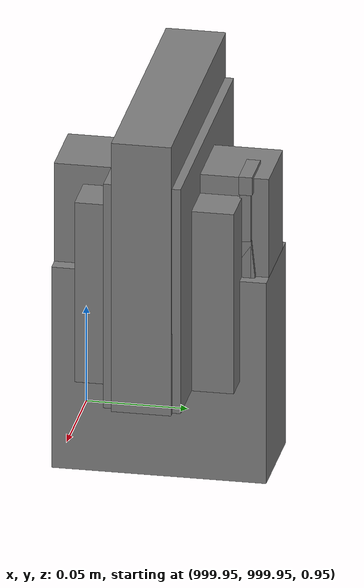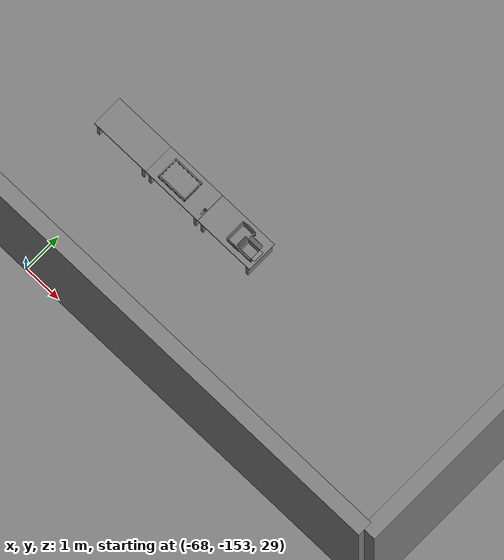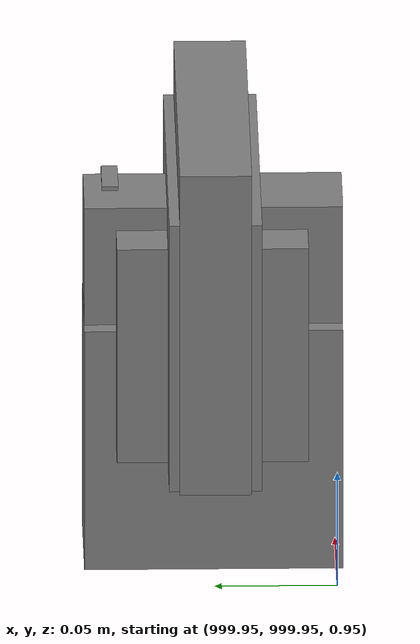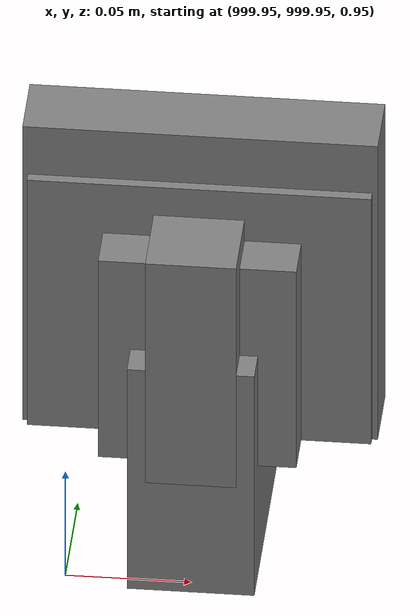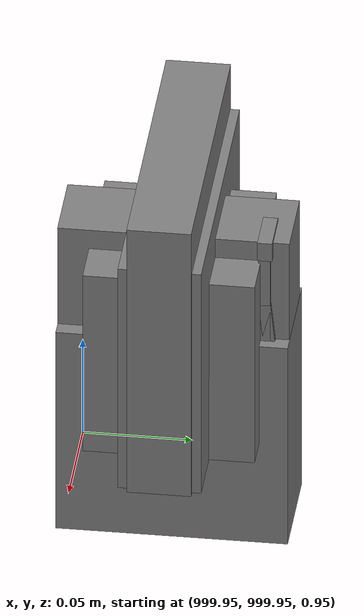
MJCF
<mujoco>
    <option gravity="0.000000000 0.000000000 -9.810000420" timestep="0.0049999999" integrator="implicitfast" density="1.225" viscosity="1.8000001e-05" noslip_iterations="10" iterations="100" sdf_iterations="50">
        <flag multiccd="disable"/>
    </option>
    <size memory="1000M"/>
    <compiler coordinate="local"/>
    <worldbody>
        <light cutoff="30" pos="0 1 1" dir="0 -1 -2"/>
        <light cutoff="30" pos="0 -1 1" dir="0 1 -2"/>
        <body pos="-64.866622925 -149.383972168 30.183746338" euler="89.999984741 89.999946594 0.000000000" name="openloong_gripper_2f85_fix_base_usda_bluebox_01">
            <geom contype="1" conaffinity="1" density="1000" type="box" material="" rgba="0.500000000 0.500000000 0.500000000 1.000000000" solimp="0.899999976 0.949999988 0.001000000" friction="1.000000000 0.005000000 0.000100000" solref="0.020000000 1.000000000" margin="0" condim="3" group="0" pos="0.276580811 0.187225342 0.000068665" quat="0.707106948 0.000077471 0.707106352 0.000077486" size="0.100000001 0.057999998 0.010000000" name="openloong_gripper_2f85_fix_base_usda_geom_9F8CFF26_21CC_4466_BE31_D3E8D67900CD"/>
            <geom contype="1" conaffinity="1" density="1000" type="box" material="" rgba="0.500000000 0.500000000 0.500000000 1.000000000" solimp="0.899999976 0.949999988 0.001000000" friction="1.000000000 0.005000000 0.000100000" solref="0.020000000 1.000000000" margin="0" condim="3" group="0" pos="0.000000000 0.002883911 0.000000000" quat="0.999999881 0.000000000 0.000000000 0.000000000" size="0.254000008 0.003000000 0.172000006" name="openloong_gripper_2f85_fix_base_usda_geom_B8864407_B2EC_4348_ACC7_689BC77E5A31"/>
            <geom contype="1" conaffinity="1" density="1000" type="box" material="" rgba="0.500000000 0.500000000 0.500000000 1.000000000" solimp="0.899999976 0.949999988 0.001000000" friction="1.000000000 0.005000000 0.000100000" solref="0.020000000 1.000000000" margin="0" condim="3" group="0" pos="0.000000000 0.124874115 0.173484802" quat="0.999796331 0.020176515 -0.000000015 0.000000030" size="0.259999990 0.119999997 0.007000000" name="openloong_gripper_2f85_fix_base_usda_geom_A297AB76_3540_4DDB_9DC1_44F6732B249C"/>
            <geom contype="1" conaffinity="1" density="1000" type="box" material="" rgba="0.500000000 0.500000000 0.500000000 1.000000000" solimp="0.899999976 0.949999988 0.001000000" friction="1.000000000 0.005000000 0.000100000" solref="0.020000000 1.000000000" margin="0" condim="3" group="0" pos="0.000000000 0.124874115 -0.173469543" quat="0.999796331 -0.020176545 -0.000000015 0.000000000" size="0.259999990 0.119999997 0.007000000" name="openloong_gripper_2f85_fix_base_usda_geom_F873B2D0_A4E4_413C_B49D_B922E88AC2D7"/>
            <geom contype="1" conaffinity="1" density="1000" type="box" material="" rgba="0.500000000 0.500000000 0.500000000 1.000000000" solimp="0.899999976 0.949999988 0.001000000" friction="1.000000000 0.005000000 0.000100000" solref="0.020000000 1.000000000" margin="0" condim="3" group="0" pos="0.000000000 0.214008331 0.188980103" quat="0.999912977 0.013176724 0.000000015 0.000000000" size="0.259999990 0.029999999 0.012500000" name="openloong_gripper_2f85_fix_base_usda_geom_0D394C6F_CD40_4D9C_9D56_C8FD9ABB7932"/>
            <geom contype="1" conaffinity="1" density="1000" type="box" material="" rgba="0.500000000 0.500000000 0.500000000 1.000000000" solimp="0.899999976 0.949999988 0.001000000" friction="1.000000000 0.005000000 0.000100000" solref="0.020000000 1.000000000" margin="0" condim="3" group="0" pos="-0.258361816 0.125289917 0.001876831" quat="0.702796936 -0.020792112 0.710783124 0.020769298" size="0.189999998 0.119999997 0.009000000" name="openloong_gripper_2f85_fix_base_usda_geom_EBF374F8_0DCC_4AAB_A7C2_A9DF865AAF8A"/>
            <geom contype="1" conaffinity="1" density="1000" type="box" material="" rgba="0.500000000 0.500000000 0.500000000 1.000000000" solimp="0.899999976 0.949999988 0.001000000" friction="1.000000000 0.005000000 0.000100000" solref="0.020000000 1.000000000" margin="0" condim="3" group="0" pos="0.000000000 0.214008331 -0.188980103" quat="0.999912977 -0.013176769 0.000000030 0.000000015" size="0.259999990 0.029999999 0.012500000" name="openloong_gripper_2f85_fix_base_usda_geom_7EF37861_46F8_4C46_835F_D212548B7955"/>
            <geom contype="1" conaffinity="1" density="1000" type="box" material="" rgba="0.500000000 0.500000000 0.500000000 1.000000000" solimp="0.899999976 0.949999988 0.001000000" friction="1.000000000 0.005000000 0.000100000" solref="0.020000000 1.000000000" margin="0" condim="3" group="0" pos="-0.276611328 0.187225342 0.000068665" quat="0.707106650 0.000077441 0.707106709 0.000077456" size="0.100000001 0.057999998 0.010000000" name="openloong_gripper_2f85_fix_base_usda_geom_B56A4CD5_DC66_4763_A0BD_B350EF74E2D2"/>
            <geom contype="1" conaffinity="1" density="1000" type="box" material="" rgba="0.500000000 0.500000000 0.500000000 1.000000000" solimp="0.899999976 0.949999988 0.001000000" friction="1.000000000 0.005000000 0.000100000" solref="0.020000000 1.000000000" margin="0" condim="3" group="0" pos="0.258331299 0.125289917 0.001876831" quat="0.702851415 0.018856421 0.710823774 -0.019329369" size="0.189999998 0.119999997 0.009000000" name="openloong_gripper_2f85_fix_base_usda_geom_010F327A_182C_45B3_AEDD_8ED28F025679"/>
            <freejoint name="openloong_gripper_2f85_fix_base_usda_bluebox_01_joint"/>
            <site size="0.005000000 0.005000000 0.005000000" rgba="0.500000000 0.500000000 0.500000000 1.000000000" pos="0.000000000 0.000000000 0.000000000" quat="0.999961913 0.008726534 0.000000000 0.000000000" group="0" type="sphere" name="openloong_gripper_2f85_fix_base_usda_bluebox_01site"/>
        </body>
        <body pos="-64.496299744 -149.491867065 30.235729218" euler="0.000000000 0.000000000 89.999946594" name="openloong_gripper_2f85_fix_base_usda_cardboardbox_01">
            <geom contype="1" conaffinity="1" density="1000" type="box" material="" rgba="0.500000000 0.500000000 0.500000000 1.000000000" solimp="0.899999976 0.949999988 0.001000000" friction="1.000000000 0.005000000 0.000100000" solref="0.020000000 1.000000000" margin="0" condim="3" group="0" pos="-0.003166199 -0.004086494 0.005052090" quat="1.000000000 0.000000000 0.000000000 0.000000000" size="0.142499998 0.177500010 0.005000000" name="openloong_gripper_2f85_fix_base_usda_geom_012BE477_11AB_486C_8C42_D2029E612336"/>
            <geom contype="1" conaffinity="1" density="1000" type="box" material="" rgba="0.500000000 0.500000000 0.500000000 1.000000000" solimp="0.899999976 0.949999988 0.001000000" friction="1.000000000 0.005000000 0.000100000" solref="0.020000000 1.000000000" margin="0" condim="3" group="0" pos="-0.003166199 0.170316696 0.150570869" quat="1.000000000 0.000000000 0.000000000 0.000000000" size="0.142499998 0.005000000 0.149999991" name="openloong_gripper_2f85_fix_base_usda_geom_87A3B1D7_8C3A_4DC5_8D60_8DDA35ED2ECB"/>
            <geom contype="1" conaffinity="1" density="1000" type="box" material="" rgba="0.500000000 0.500000000 0.500000000 1.000000000" solimp="0.899999976 0.949999988 0.001000000" friction="1.000000000 0.005000000 0.000100000" solref="0.020000000 1.000000000" margin="0" condim="3" group="0" pos="-0.147399902 -0.005307198 0.150570869" quat="1.000000000 0.000000000 0.000000000 0.000000000" size="0.005000000 0.177500010 0.149999991" name="openloong_gripper_2f85_fix_base_usda_geom_ABDBFAD4_A25B_4C9F_8C06_748FA24EC917"/>
            <geom contype="1" conaffinity="1" density="1000" type="box" material="" rgba="0.500000000 0.500000000 0.500000000 1.000000000" solimp="0.899999976 0.949999988 0.001000000" friction="1.000000000 0.005000000 0.000100000" solref="0.020000000 1.000000000" margin="0" condim="3" group="0" pos="0.140275955 -0.005307198 0.150570869" quat="1.000000000 0.000000000 0.000000000 0.000000000" size="0.005000000 0.177500010 0.149999991" name="openloong_gripper_2f85_fix_base_usda_geom_BF158FD0_9B8E_4366_8CB8_D9BC60D25DFF"/>
            <geom contype="1" conaffinity="1" density="1000" type="box" material="" rgba="0.500000000 0.500000000 0.500000000 1.000000000" solimp="0.899999976 0.949999988 0.001000000" friction="1.000000000 0.005000000 0.000100000" solref="0.020000000 1.000000000" margin="0" condim="3" group="0" pos="-0.003166199 -0.181550980 0.150570869" quat="1.000000000 0.000000000 0.000000000 0.000000000" size="0.142499998 0.005000000 0.149999991" name="openloong_gripper_2f85_fix_base_usda_geom_9E2C41AB_0D19_4C4F_8E0D_3B9B2AFE4B78"/>
            <freejoint name="openloong_gripper_2f85_fix_base_usda_cardboardbox_01_joint"/>
            <site size="0.005000000 0.005000000 0.005000000" rgba="0.500000000 0.500000000 0.500000000 1.000000000" pos="0.000000000 0.000000000 0.000000000" quat="0.999961913 0.008726535 0.000000000 0.000000000" group="0" type="sphere" name="openloong_gripper_2f85_fix_base_usda_site_831DECC9_439F_46B7_89FC_4329FFC9F756"/>
            <body pos="0.139160156 -0.004048347 0.301930904" euler="-179.999954224 49.383502960 179.999954224" name="openloong_gripper_2f85_fix_base_usda_A1_006">
                <geom contype="1" conaffinity="1" density="1000" type="box" material="" rgba="0.500000000 0.500000000 0.500000000 1.000000000" solimp="0.899999976 0.949999988 0.001000000" friction="1.000000000 0.005000000 0.000100000" solref="0.020000000 1.000000000" margin="0" condim="3" group="0" pos="-0.071587563 0.000009537 0.001745224" quat="0.999999881 0.000000000 0.000000000 0.000000000" size="0.071249999 0.179999992 0.002500000" name="openloong_gripper_2f85_fix_base_usda_geom_B03EAFC2_7D10_4FA2_A4D4_A3EDA14FFFB9"/>
                <joint armature="0" stiffness="0.07" damping="0.0099999998" axis="0.000000 1.000000 0.000000" type="hinge" name="openloong_gripper_2f85_fix_base_usda_A1_006"/>
            </body>
            <body pos="-0.145902634 -0.004086494 0.301938057" euler="-180.000000000 -60.000011444 -180.000000000" name="openloong_gripper_2f85_fix_base_usda_A2_006">
                <geom contype="1" conaffinity="1" density="1000" type="box" material="" rgba="0.500000000 0.500000000 0.500000000 1.000000000" solimp="0.899999976 0.949999988 0.001000000" friction="1.000000000 0.005000000 0.000100000" solref="0.020000000 1.000000000" margin="0" condim="3" group="0" pos="0.071268082 0.000009537 0.002717972" quat="0.000002921 0.000000000 -0.000000030 0.999999881" size="0.071249999 0.179999992 0.002500000" name="openloong_gripper_2f85_fix_base_usda_geom_E486EA52_BD54_405A_B963_81002952662D"/>
                <joint armature="0" stiffness="0.07" damping="0.0099999998" axis="0.000000 1.000000 0.000000" type="hinge" name="openloong_gripper_2f85_fix_base_usda_A2_006"/>
            </body>
            <body pos="-0.003385544 0.175991058 0.301930904" euler="-125.858116150 -0.000004561 0.000002331" name="openloong_gripper_2f85_fix_base_usda_B2_006">
                <geom contype="1" conaffinity="1" density="1000" type="box" material="" rgba="0.500000000 0.500000000 0.500000000 1.000000000" solimp="0.899999976 0.949999988 0.001000000" friction="1.000000000 0.005000000 0.000100000" solref="0.020000000 1.000000000" margin="0" condim="3" group="0" pos="0.000009537 -0.070939064 -0.002470016" quat="0.999614120 0.027776197 -0.000000015 0.000000030" size="0.137500003 0.064999998 0.005000000" name="openloong_gripper_2f85_fix_base_usda_geom_72ED4B10_8DBC_4BF7_AAF5_2B61D4A2F801"/>
                <joint armature="0" stiffness="0.07" damping="0.0099999998" axis="1.000000 0.000000 0.000000" type="hinge" name="openloong_gripper_2f85_fix_base_usda_B2_006"/>
            </body>
            <body pos="-0.003385544 -0.184140205 0.301938057" euler="147.805557251 0.000000000 0.000000000" name="openloong_gripper_2f85_fix_base_usda_B1_006">
                <geom contype="1" conaffinity="1" density="1000" type="box" material="" rgba="0.500000000 0.500000000 0.500000000 1.000000000" solimp="0.899999976 0.949999988 0.001000000" friction="1.000000000 0.005000000 0.000100000" solref="0.020000000 1.000000000" margin="0" condim="3" group="0" pos="-0.000028610 0.070202351 -0.002703667" quat="0.999614179 -0.027776167 0.000000000 0.000000000" size="0.137500003 0.064999998 0.005000000" name="openloong_gripper_2f85_fix_base_usda_geom_6D748561_F9AC_43A1_9507_1961B951DA67"/>
                <joint armature="0" stiffness="0.07" damping="0.0099999998" axis="1.000000 0.000000 0.000000" type="hinge" name="openloong_gripper_2f85_fix_base_usda_B1_006"/>
            </body>
        </body>
        <body pos="-65.882858276 -149.481979370 30.229999542" euler="-64.487716675 0.000000000 0.000000000" name="openloong_gripper_2f85_fix_base_usda_Barcode">
            <geom contype="1" conaffinity="1" density="1000" type="box" material="" rgba="0.500000000 0.500000000 0.500000000 1.000000000" solimp="0.899999976 0.949999988 0.001000000" friction="1.000000000 0.005000000 0.000100000" solref="0.020000000 1.000000000" margin="0" condim="3" group="0" pos="0.000000000 0.013038635 0.001419067" quat="0.000000000 0.000000000 0.000000000 1.000000119" size="0.034000002 0.010000000 0.017999999" name="openloong_gripper_2f85_fix_base_usda_geom_8EC7FC08_754D_4441_96B7_15205CF4A322"/>
            <geom contype="1" conaffinity="1" density="1000" type="box" material="" rgba="0.500000000 0.500000000 0.500000000 1.000000000" solimp="0.899999976 0.949999988 0.001000000" friction="1.000000000 0.005000000 0.000100000" solref="0.020000000 1.000000000" margin="0" condim="3" group="0" pos="0.000000000 -0.035301208 -0.007095337" quat="0.000000000 0.000000000 -0.043619365 0.999048233" size="0.028999999 0.010000000 0.020000000" name="openloong_gripper_2f85_fix_base_usda_geom_BD261BA9_500F_498C_936A_B7D11765D492"/>
            <geom contype="1" conaffinity="1" density="1000" type="box" material="" rgba="0.500000000 0.500000000 0.500000000 1.000000000" solimp="0.899999976 0.949999988 0.001000000" friction="1.000000000 0.005000000 0.000100000" solref="0.020000000 1.000000000" margin="0" condim="3" group="0" pos="0.000000000 -0.043411255 -0.011749268" quat="0.922262907 0.386563420 0.000000000 0.000000000" size="0.026000001 0.010000000 0.020000000" name="openloong_gripper_2f85_fix_base_usda_geom_68CD2F3F_8260_4ADC_B9F2_48771F5E261A"/>
            <geom contype="1" conaffinity="1" density="1000" type="box" material="" rgba="0.500000000 0.500000000 0.500000000 1.000000000" solimp="0.899999976 0.949999988 0.001000000" friction="1.000000000 0.005000000 0.000100000" solref="0.020000000 1.000000000" margin="0" condim="3" group="0" pos="0.000000000 -0.016967773 -0.031860352" quat="0.000000000 0.000000000 0.000000000 1.000000119" size="0.008000000 0.010000000 0.013000000" name="openloong_gripper_2f85_fix_base_usda_geom_FCA686F2_F00B_4A37_8FC3_AB2C4A5EC84F"/>
            <geom contype="1" conaffinity="1" density="1000" type="box" material="" rgba="0.500000000 0.500000000 0.500000000 1.000000000" solimp="0.899999976 0.949999988 0.001000000" friction="1.000000000 0.005000000 0.000100000" solref="0.020000000 1.000000000" margin="0" condim="3" group="0" pos="0.000000000 -0.001869202 0.000312805" quat="0.953716993 0.300705761 0.000000000 0.000000000" size="0.032000002 0.010000000 0.018999999" name="openloong_gripper_2f85_fix_base_usda_geom_C4F524E1_B576_4844_97A2_4EDD91A94414"/>
            <geom contype="1" conaffinity="1" density="1000" type="box" material="" rgba="0.500000000 0.500000000 0.500000000 1.000000000" solimp="0.899999976 0.949999988 0.001000000" friction="1.000000000 0.005000000 0.000100000" solref="0.020000000 1.000000000" margin="0" condim="3" group="0" pos="0.000000000 -0.019531250 -0.003173828" quat="0.953716993 0.300705761 0.000000000 0.000000000" size="0.030999999 0.010000000 0.020000000" name="openloong_gripper_2f85_fix_base_usda_geom_D9BA2D80_1A99_4FDA_A219_204FBF1802B5"/>
            <geom contype="1" conaffinity="1" density="1000" type="box" material="" rgba="0.500000000 0.500000000 0.500000000 1.000000000" solimp="0.899999976 0.949999988 0.001000000" friction="1.000000000 0.005000000 0.000100000" solref="0.020000000 1.000000000" margin="0" condim="3" group="0" pos="0.000000000 -0.035301208 -0.007095337" quat="0.953716993 0.300705761 0.000000000 0.000000000" size="0.028999999 0.010000000 0.020000000" name="openloong_gripper_2f85_fix_base_usda_geom_D03A4E09_B031_4C16_BFD2_50F5821C5CEB"/>
            <geom contype="1" conaffinity="1" density="1000" type="box" material="" rgba="0.500000000 0.500000000 0.500000000 1.000000000" solimp="0.899999976 0.949999988 0.001000000" friction="1.000000000 0.005000000 0.000100000" solref="0.020000000 1.000000000" margin="0" condim="3" group="0" pos="0.000000000 -0.042617798 -0.071121216" quat="0.000000000 0.000000000 0.000000000 1.000000119" size="0.013000000 0.021000000 0.059999999" name="openloong_gripper_2f85_fix_base_usda_geom_FD07B1A6_06C8_4B0F_B442_A6CE6A5AFDA8"/>
            <freejoint name="openloong_gripper_2f85_fix_base_usda_Barcode_joint"/>
            <site size="0.005000000 0.005000000 0.005000000" rgba="0.500000000 0.500000000 0.500000000 1.000000000" pos="0.000000000 0.000000000 0.000000000" quat="1.000000000 0.000000000 0.000000000 0.000000000" group="0" type="sphere" name="openloong_gripper_2f85_fix_base_usda_Barcode_site"/>
        </body>
        <body pos="-66.745018005 -149.392349243 30.184000015" euler="0.000000000 0.000000000 89.999946594" name="[22332501028280]_Basket_01">
            <geom contype="1" conaffinity="1" density="1000" type="box" material="" rgba="0.500000000 0.500000000 0.500000000 1.000000000" solimp="0.899999976 0.949999988 0.001000000" friction="1.000000000 0.005000000 0.000100000" solref="0.020000000 1.000000000" margin="0" condim="3" group="0" pos="-0.052425385 0.389207840 0.089787483" quat="0.707107008 0.000000000 0.000000000 0.707106411" size="0.014249999 0.014249999 0.059999999" name="[22332501028280]_geom_5C2CB8C5_5AD9_4AA1_8948_A4978B3C4EFD"/>
            <geom contype="1" conaffinity="1" density="1000" type="box" material="" rgba="0.500000000 0.500000000 0.500000000 1.000000000" solimp="0.899999976 0.949999988 0.001000000" friction="1.000000000 0.005000000 0.000100000" solref="0.020000000 1.000000000" margin="0" condim="3" group="0" pos="0.264015198 -0.133043289 0.089787483" quat="0.707107008 0.000000000 0.000000000 0.707106411" size="0.014249999 0.014249999 0.059999999" name="[22332501028280]_geom_05184FC8_4AB9_4321_B300_22539061C063"/>
            <geom contype="1" conaffinity="1" density="1000" type="box" material="" rgba="0.500000000 0.500000000 0.500000000 1.000000000" solimp="0.899999976 0.949999988 0.001000000" friction="1.000000000 0.005000000 0.000100000" solref="0.020000000 1.000000000" margin="0" condim="3" group="0" pos="-0.264015198 -0.265548706 0.089793205" quat="0.707107008 0.000000000 0.000000000 0.707106411" size="0.014249999 0.014249999 0.059999999" name="[22332501028280]_geom_3D45B2F9_6216_4C1F_BEC9_C2A7AFC595FB"/>
            <geom contype="1" conaffinity="1" density="1000" type="box" material="" rgba="0.500000000 0.500000000 0.500000000 1.000000000" solimp="0.899999976 0.949999988 0.001000000" friction="1.000000000 0.005000000 0.000100000" solref="0.020000000 1.000000000" margin="0" condim="3" group="0" pos="-0.160263062 -0.389322281 0.089793205" quat="0.707107008 0.000000000 0.000000000 0.707106411" size="0.014249999 0.014249999 0.059999999" name="[22332501028280]_geom_74BF2AFF_1DC5_489F_AD79_505BDFAD4409"/>
            <geom contype="1" conaffinity="1" density="1000" type="box" material="" rgba="0.500000000 0.500000000 0.500000000 1.000000000" solimp="0.899999976 0.949999988 0.001000000" friction="1.000000000 0.005000000 0.000100000" solref="0.020000000 1.000000000" margin="0" condim="3" group="0" pos="0.162265778 -0.389322281 0.089787483" quat="0.707107008 0.000000000 0.000000000 0.707106411" size="0.014249999 0.014249999 0.059999999" name="[22332501028280]_geom_6040B743_501C_46F1_B178_EDA1F40A7A27"/>
            <geom contype="1" conaffinity="1" density="1000" type="box" material="" rgba="0.500000000 0.500000000 0.500000000 1.000000000" solimp="0.899999976 0.949999988 0.001000000" friction="1.000000000 0.005000000 0.000100000" solref="0.020000000 1.000000000" margin="0" condim="3" group="0" pos="0.264015198 0.389207840 0.089787483" quat="0.707107008 0.000000000 0.000000000 0.707106411" size="0.014249999 0.014249999 0.059999999" name="[22332501028280]_geom_5BD25641_885A_4DC6_B0FB_D8FF33ACAA13"/>
            <geom contype="1" conaffinity="1" density="1000" type="box" material="" rgba="0.500000000 0.500000000 0.500000000 1.000000000" solimp="0.899999976 0.949999988 0.001000000" friction="1.000000000 0.005000000 0.000100000" solref="0.020000000 1.000000000" margin="0" condim="3" group="0" pos="-0.264015198 -0.133043289 0.089793205" quat="0.707107008 0.000000000 0.000000000 0.707106411" size="0.014249999 0.014249999 0.059999999" name="[22332501028280]_geom_28BECF6B_B637_480C_A5C9_A56241F98241"/>
            <geom contype="1" conaffinity="1" density="1000" type="box" material="" rgba="0.500000000 0.500000000 0.500000000 1.000000000" solimp="0.899999976 0.949999988 0.001000000" friction="1.000000000 0.005000000 0.000100000" solref="0.020000000 1.000000000" margin="0" condim="3" group="0" pos="-0.264026642 0.269256592 0.089793205" quat="0.707107008 0.000000000 0.000000000 0.707106411" size="0.014249999 0.014249999 0.059999999" name="[22332501028280]_geom_5FB6804F_E7EB_4EC1_9AD0_DA04F9EED28A"/>
            <geom contype="1" conaffinity="1" density="1000" type="box" material="" rgba="0.500000000 0.500000000 0.500000000 1.000000000" solimp="0.899999976 0.949999988 0.001000000" friction="1.000000000 0.005000000 0.000100000" solref="0.020000000 1.000000000" margin="0" condim="3" group="0" pos="0.054462433 0.389207840 0.089787483" quat="0.707107008 0.000000000 0.000000000 0.707106411" size="0.014249999 0.014249999 0.059999999" name="[22332501028280]_geom_19BA5647_469F_42B3_9104_0B50DB4C4B66"/>
            <geom contype="1" conaffinity="1" density="1000" type="box" material="" rgba="0.500000000 0.500000000 0.500000000 1.000000000" solimp="0.899999976 0.949999988 0.001000000" friction="1.000000000 0.005000000 0.000100000" solref="0.020000000 1.000000000" margin="0" condim="3" group="0" pos="0.054462433 -0.389322281 0.089787483" quat="0.707107008 0.000000000 0.000000000 0.707106411" size="0.014249999 0.014249999 0.059999999" name="[22332501028280]_geom_4C1D3FCA_6971_4025_97C7_75423192EE3C"/>
            <geom contype="1" conaffinity="1" density="1000" type="box" material="" rgba="0.500000000 0.500000000 0.500000000 1.000000000" solimp="0.899999976 0.949999988 0.001000000" friction="1.000000000 0.005000000 0.000100000" solref="0.020000000 1.000000000" margin="0" condim="3" group="0" pos="0.264015198 0.269256592 0.089793205" quat="0.707107008 0.000000000 0.000000000 0.707106411" size="0.014249999 0.014249999 0.059999999" name="[22332501028280]_geom_03A06F57_EBD0_49B2_B62C_45F65ED715ED"/>
            <geom contype="1" conaffinity="1" density="1000" type="box" material="" rgba="0.500000000 0.500000000 0.500000000 1.000000000" solimp="0.899999976 0.949999988 0.001000000" friction="1.000000000 0.005000000 0.000100000" solref="0.020000000 1.000000000" margin="0" condim="3" group="0" pos="0.264015198 -0.389322281 0.089787483" quat="0.707107008 0.000000000 0.000000000 0.707106411" size="0.014249999 0.014249999 0.059999999" name="[22332501028280]_geom_5F5A94DC_D1CB_4875_BF3C_D997D555AB12"/>
            <geom contype="1" conaffinity="1" density="1000" type="box" material="" rgba="0.500000000 0.500000000 0.500000000 1.000000000" solimp="0.899999976 0.949999988 0.001000000" friction="1.000000000 0.005000000 0.000100000" solref="0.020000000 1.000000000" margin="0" condim="3" group="0" pos="0.000000000 0.000000000 0.015998840" quat="0.707107008 0.000000000 0.000000000 0.707106411" size="0.403499991 0.279000014 0.015750000" name="[22332501028280]_geom_C0A9C6A3_3D13_4C66_8920_19B2A91B0376"/>
            <geom contype="1" conaffinity="1" density="1000" type="box" material="" rgba="0.500000000 0.500000000 0.500000000 1.000000000" solimp="0.899999976 0.949999988 0.001000000" friction="1.000000000 0.005000000 0.000100000" solref="0.020000000 1.000000000" margin="0" condim="3" group="0" pos="0.000000000 -0.389476776 0.163619041" quat="0.707107008 0.000000000 0.000000000 0.707106411" size="0.015000000 0.277500004 0.015750000" name="[22332501028280]_geom_660766B9_51A5_4198_8BB6_ACB44F4B360B"/>
            <geom contype="1" conaffinity="1" density="1000" type="box" material="" rgba="0.500000000 0.500000000 0.500000000 1.000000000" solimp="0.899999976 0.949999988 0.001000000" friction="1.000000000 0.005000000 0.000100000" solref="0.020000000 1.000000000" margin="0" condim="3" group="0" pos="0.162265778 0.389207840 0.089787483" quat="0.707107008 0.000000000 0.000000000 0.707106411" size="0.014249999 0.014249999 0.059999999" name="[22332501028280]_geom_363FE991_E23D_4998_BE75_FC46033F6F8A"/>
            <geom contype="1" conaffinity="1" density="1000" type="box" material="" rgba="0.500000000 0.500000000 0.500000000 1.000000000" solimp="0.899999976 0.949999988 0.001000000" friction="1.000000000 0.005000000 0.000100000" solref="0.020000000 1.000000000" margin="0" condim="3" group="0" pos="0.000000000 0.389471054 0.163619041" quat="0.707107008 0.000000000 0.000000000 0.707106411" size="0.015000000 0.277500004 0.015750000" name="[22332501028280]_geom_E699216E_BDA2_4564_AE41_4E2AA39ECD0D"/>
            <geom contype="1" conaffinity="1" density="1000" type="box" material="" rgba="0.500000000 0.500000000 0.500000000 1.000000000" solimp="0.899999976 0.949999988 0.001000000" friction="1.000000000 0.005000000 0.000100000" solref="0.020000000 1.000000000" margin="0" condim="3" group="0" pos="-0.263511658 0.000000000 0.163619041" quat="0.707107008 0.000000000 0.000000000 0.707106411" size="0.403499991 0.015000000 0.015750000" name="[22332501028280]_geom_F32A098B_7028_46C1_8F9A_C19AA3669EB3"/>
            <geom contype="1" conaffinity="1" density="1000" type="box" material="" rgba="0.500000000 0.500000000 0.500000000 1.000000000" solimp="0.899999976 0.949999988 0.001000000" friction="1.000000000 0.005000000 0.000100000" solref="0.020000000 1.000000000" margin="0" condim="3" group="0" pos="-0.264015198 0.141334534 0.089793205" quat="0.707107008 0.000000000 0.000000000 0.707106411" size="0.014249999 0.014249999 0.059999999" name="[22332501028280]_geom_06B02DBD_D2BE_411D_8080_49C09820D2CC"/>
            <geom contype="1" conaffinity="1" density="1000" type="box" material="" rgba="0.500000000 0.500000000 0.500000000 1.000000000" solimp="0.899999976 0.949999988 0.001000000" friction="1.000000000 0.005000000 0.000100000" solref="0.020000000 1.000000000" margin="0" condim="3" group="0" pos="0.264015198 -0.265548706 0.089787483" quat="0.707107008 0.000000000 0.000000000 0.707106411" size="0.014249999 0.014249999 0.059999999" name="[22332501028280]_geom_570F6A67_0AF2_462D_B543_F5377126A385"/>
            <geom contype="1" conaffinity="1" density="1000" type="box" material="" rgba="0.500000000 0.500000000 0.500000000 1.000000000" solimp="0.899999976 0.949999988 0.001000000" friction="1.000000000 0.005000000 0.000100000" solref="0.020000000 1.000000000" margin="0" condim="3" group="0" pos="-0.160263062 0.389207840 0.089787483" quat="0.707107008 0.000000000 0.000000000 0.707106411" size="0.014249999 0.014249999 0.059999999" name="[22332501028280]_geom_6188F14D_9B35_4CEF_BD59_26AEDCEBE6CC"/>
            <geom contype="1" conaffinity="1" density="1000" type="box" material="" rgba="0.500000000 0.500000000 0.500000000 1.000000000" solimp="0.899999976 0.949999988 0.001000000" friction="1.000000000 0.005000000 0.000100000" solref="0.020000000 1.000000000" margin="0" condim="3" group="0" pos="-0.052425385 -0.389322281 0.089787483" quat="0.707107008 0.000000000 0.000000000 0.707106411" size="0.014249999 0.014249999 0.059999999" name="[22332501028280]_geom_E164D2E5_7806_40E5_9132_57B2679B88A3"/>
            <geom contype="1" conaffinity="1" density="1000" type="box" material="" rgba="0.500000000 0.500000000 0.500000000 1.000000000" solimp="0.899999976 0.949999988 0.001000000" friction="1.000000000 0.005000000 0.000100000" solref="0.020000000 1.000000000" margin="0" condim="3" group="0" pos="-0.264026642 -0.389322281 0.089793205" quat="0.707107008 0.000000000 0.000000000 0.707106411" size="0.014249999 0.014249999 0.059999999" name="[22332501028280]_geom_A1149CE5_4836_48AE_A177_EE6F18B57DEC"/>
            <geom contype="1" conaffinity="1" density="1000" type="box" material="" rgba="0.500000000 0.500000000 0.500000000 1.000000000" solimp="0.899999976 0.949999988 0.001000000" friction="1.000000000 0.005000000 0.000100000" solref="0.020000000 1.000000000" margin="0" condim="3" group="0" pos="0.264015198 0.141334534 0.089787483" quat="0.707107008 0.000000000 0.000000000 0.707106411" size="0.014249999 0.014249999 0.059999999" name="[22332501028280]_geom_11C773BC_BD8B_4F03_92C1_D6CC5FEEC9B6"/>
            <geom contype="1" conaffinity="1" density="1000" type="box" material="" rgba="0.500000000 0.500000000 0.500000000 1.000000000" solimp="0.899999976 0.949999988 0.001000000" friction="1.000000000 0.005000000 0.000100000" solref="0.020000000 1.000000000" margin="0" condim="3" group="0" pos="-0.264015198 0.389207840 0.089793205" quat="0.707107008 0.000000000 0.000000000 0.707106411" size="0.014249999 0.014249999 0.059999999" name="[22332501028280]_geom_BB730B74_F535_44C6_AFCB_BF04F210C5AE"/>
            <geom contype="1" conaffinity="1" density="1000" type="box" material="" rgba="0.500000000 0.500000000 0.500000000 1.000000000" solimp="0.899999976 0.949999988 0.001000000" friction="1.000000000 0.005000000 0.000100000" solref="0.020000000 1.000000000" margin="0" condim="3" group="0" pos="0.264015198 0.004480362 0.089787483" quat="0.707107008 0.000000000 0.000000000 0.707106411" size="0.014249999 0.014249999 0.059999999" name="[22332501028280]_geom_21BA36E2_6E5E_4212_A315_1DF0E93FD3A6"/>
            <geom contype="1" conaffinity="1" density="1000" type="box" material="" rgba="0.500000000 0.500000000 0.500000000 1.000000000" solimp="0.899999976 0.949999988 0.001000000" friction="1.000000000 0.005000000 0.000100000" solref="0.020000000 1.000000000" margin="0" condim="3" group="0" pos="0.263694763 -0.000011444 0.163619041" quat="0.707107008 0.000000000 0.000000000 0.707106411" size="0.403499991 0.015000000 0.015750000" name="[22332501028280]_geom_C23523AF_352A_4A89_98B1_F25835F8A6CC"/>
            <geom contype="1" conaffinity="1" density="1000" type="box" material="" rgba="0.500000000 0.500000000 0.500000000 1.000000000" solimp="0.899999976 0.949999988 0.001000000" friction="1.000000000 0.005000000 0.000100000" solref="0.020000000 1.000000000" margin="0" condim="3" group="0" pos="-0.264015198 0.004480362 0.089793205" quat="0.707107008 0.000000000 0.000000000 0.707106411" size="0.014249999 0.014249999 0.059999999" name="[22332501028280]_geom_96846510_E1D0_43D2_9B20_0837DC02DEF7"/>
            <freejoint name="[22332501028280]_joint_64212510_C561_4FB9_9322_FBB883C541D5"/>
        </body>
        <body pos="0.000000000 0.000000000 0.000000000" euler="0.000000000 0.000000000 0.000000000" name="Static Objects_Static Objects">
            <geom contype="1" conaffinity="1" density="1000" type="box" material="" rgba="0.500000000 0.500000000 0.500000000 1.000000000" solimp="0.899999976 0.949999988 0.001000000" friction="1.000000000 0.005000000 0.000100000" solref="0.020000000 1.000000000" margin="0" condim="3" group="0" pos="-67.544113159 -149.365814209 29.727830887" quat="0.500000417 0.499999970 0.499999553 0.499999970" size="0.381000012 0.319999993 0.041000001" name="Static Objects_geom_73204724_46B1_4132_BB31_38B3EBA05E4A"/>
            <geom contype="1" conaffinity="1" density="1000" type="box" material="" rgba="0.500000000 0.500000000 0.500000000 1.000000000" solimp="0.899999976 0.949999988 0.001000000" friction="1.000000000 0.005000000 0.000100000" solref="0.020000000 1.000000000" margin="0" condim="3" group="0" pos="-68.239501953 -149.365814209 30.086868286" quat="0.500000417 0.499999970 0.499999553 0.499999970" size="0.370999992 0.039500002 0.745000005" name="Static Objects_geom_19A11974_6769_4CE8_9273_A2B039B3B20D"/>
            <geom contype="1" conaffinity="1" density="1000" type="box" material="" rgba="0.500000000 0.500000000 0.500000000 1.000000000" solimp="0.899999976 0.949999988 0.001000000" friction="1.000000000 0.005000000 0.000100000" solref="0.020000000 1.000000000" margin="0" condim="3" group="0" pos="-68.239501953 -149.365814209 30.147235870" quat="0.500000417 0.499999970 0.499999553 0.499999970" size="0.400000006 0.022000000 0.800000012" name="Static Objects_geom_F589886D_0272_4888_B7D1_B943074FDECA"/>
            <geom contype="1" conaffinity="1" density="1000" type="box" material="" rgba="0.500000000 0.500000000 0.500000000 1.000000000" solimp="0.899999976 0.949999988 0.001000000" friction="1.000000000 0.005000000 0.000100000" solref="0.020000000 1.000000000" margin="0" condim="3" group="0" pos="-68.934890747 -149.365814209 29.727830887" quat="0.500000417 0.499999970 0.499999553 0.499999970" size="0.381000012 0.319999993 0.041000001" name="Static Objects_geom_93B312E6_9CF2_4ABE_9982_AA2ED475E2AE"/>
            <geom contype="1" conaffinity="1" density="1000" type="box" material="" rgba="0.500000000 0.500000000 0.500000000 1.000000000" solimp="0.899999976 0.949999988 0.001000000" friction="1.000000000 0.005000000 0.000100000" solref="0.020000000 1.000000000" margin="0" condim="3" group="0" pos="-68.239501953 -149.365814209 29.561563492" quat="0.500000417 0.499999970 0.499999553 0.499999970" size="0.020000000 0.022000000 0.660000026" name="Static Objects_geom_1B4025C7_0369_47D0_839C_3B42DB009876"/>
            <geom contype="1" conaffinity="1" density="1000" type="box" material="" rgba="0.500000000 0.500000000 0.500000000 1.000000000" solimp="0.899999976 0.949999988 0.001000000" friction="1.000000000 0.005000000 0.000100000" solref="0.020000000 1.000000000" margin="0" condim="3" group="0" pos="-65.945671082 -149.365814209 29.727830887" quat="0.500000417 0.499999970 0.499999553 0.499999970" size="0.381000012 0.319999993 0.041000001" name="Static Objects_geom_2667422E_2C2A_47C6_99FB_1504542473C8"/>
            <geom contype="1" conaffinity="1" density="1000" type="box" material="" rgba="0.500000000 0.500000000 0.500000000 1.000000000" solimp="0.899999976 0.949999988 0.001000000" friction="1.000000000 0.005000000 0.000100000" solref="0.020000000 1.000000000" margin="0" condim="3" group="0" pos="-66.641059875 -149.365814209 30.086868286" quat="0.500000417 0.499999970 0.499999553 0.499999970" size="0.370999992 0.039500002 0.745000005" name="Static Objects_geom_728583C1_22E5_4279_B46A_1AC8EB5A8E76"/>
            <geom contype="1" conaffinity="1" density="1000" type="box" material="" rgba="0.500000000 0.500000000 0.500000000 1.000000000" solimp="0.899999976 0.949999988 0.001000000" friction="1.000000000 0.005000000 0.000100000" solref="0.020000000 1.000000000" margin="0" condim="3" group="0" pos="-66.641059875 -149.365814209 30.147235870" quat="0.500000417 0.499999970 0.499999553 0.499999970" size="0.400000006 0.022000000 0.800000012" name="Static Objects_geom_E4B3741A_C691_4A1F_88A4_30340E805E9D"/>
            <geom contype="1" conaffinity="1" density="1000" type="box" material="" rgba="0.500000000 0.500000000 0.500000000 1.000000000" solimp="0.899999976 0.949999988 0.001000000" friction="1.000000000 0.005000000 0.000100000" solref="0.020000000 1.000000000" margin="0" condim="3" group="0" pos="-67.336448669 -149.365814209 29.727830887" quat="0.500000417 0.499999970 0.499999553 0.499999970" size="0.381000012 0.319999993 0.041000001" name="Static Objects_geom_4A4AD3F4_9FB4_41AF_B7A2_4F42EFF55AE3"/>
            <geom contype="1" conaffinity="1" density="1000" type="box" material="" rgba="0.500000000 0.500000000 0.500000000 1.000000000" solimp="0.899999976 0.949999988 0.001000000" friction="1.000000000 0.005000000 0.000100000" solref="0.020000000 1.000000000" margin="0" condim="3" group="0" pos="-66.641059875 -149.365814209 29.561563492" quat="0.500000417 0.499999970 0.499999553 0.499999970" size="0.020000000 0.022000000 0.660000026" name="Static Objects_geom_330000C5_7CFD_4C37_929E_286EA6B7659D"/>
            <geom contype="1" conaffinity="1" density="1000" type="box" material="" rgba="0.500000000 0.500000000 0.500000000 1.000000000" solimp="0.899999976 0.949999988 0.001000000" friction="1.000000000 0.005000000 0.000100000" solref="0.020000000 1.000000000" margin="0" condim="3" group="0" pos="-64.338577271 -149.365814209 29.727830887" quat="0.500000417 0.499999970 0.499999553 0.499999970" size="0.381000012 0.319999993 0.041000001" name="Static Objects_geom_41066914_A1CE_4128_992C_0D73CC2676B4"/>
            <geom contype="1" conaffinity="1" density="1000" type="box" material="" rgba="0.500000000 0.500000000 0.500000000 1.000000000" solimp="0.899999976 0.949999988 0.001000000" friction="1.000000000 0.005000000 0.000100000" solref="0.020000000 1.000000000" margin="0" condim="3" group="0" pos="-65.033966064 -149.365814209 30.086868286" quat="0.500000417 0.499999970 0.499999553 0.499999970" size="0.370999992 0.039500002 0.745000005" name="Static Objects_geom_6E0CF7EE_42E2_4B17_90C0_E2D775345526"/>
            <geom contype="1" conaffinity="1" density="1000" type="box" material="" rgba="0.500000000 0.500000000 0.500000000 1.000000000" solimp="0.899999976 0.949999988 0.001000000" friction="1.000000000 0.005000000 0.000100000" solref="0.020000000 1.000000000" margin="0" condim="3" group="0" pos="-65.033966064 -149.365814209 30.147235870" quat="0.500000417 0.499999970 0.499999553 0.499999970" size="0.400000006 0.022000000 0.800000012" name="Static Objects_geom_784C620D_D00F_426E_9DA1_AE1C0C749B60"/>
            <geom contype="1" conaffinity="1" density="1000" type="box" material="" rgba="0.500000000 0.500000000 0.500000000 1.000000000" solimp="0.899999976 0.949999988 0.001000000" friction="1.000000000 0.005000000 0.000100000" solref="0.020000000 1.000000000" margin="0" condim="3" group="0" pos="-65.729354858 -149.365814209 29.727830887" quat="0.500000417 0.499999970 0.499999553 0.499999970" size="0.381000012 0.319999993 0.041000001" name="Static Objects_geom_BB446965_CC4B_4055_850E_CD67DF06F482"/>
            <geom contype="1" conaffinity="1" density="1000" type="box" material="" rgba="0.500000000 0.500000000 0.500000000 1.000000000" solimp="0.899999976 0.949999988 0.001000000" friction="1.000000000 0.005000000 0.000100000" solref="0.020000000 1.000000000" margin="0" condim="3" group="0" pos="-65.033966064 -149.365814209 29.561563492" quat="0.500000417 0.499999970 0.499999553 0.499999970" size="0.020000000 0.022000000 0.660000026" name="Static Objects_geom_5FB050DD_F365_467D_AC76_C6AAE8654316"/>
            <geom contype="1" conaffinity="1" density="1000" type="box" material="" rgba="0.500000000 0.500000000 0.500000000 1.000000000" solimp="0.899999976 0.949999988 0.001000000" friction="1.000000000 0.005000000 0.000100000" solref="0.020000000 1.000000000" margin="0" condim="3" group="0" pos="-61.754566193 -137.853729248 33.906845093" quat="0.707107067 0.000000000 0.000000000 0.707106471" size="0.759999990 0.759999990 4.500000000" name="Static Objects_geom_EADC5A3E_9A7E_49B4_948F_8DD6D972996F"/>
            <geom contype="1" conaffinity="1" density="1000" type="box" material="" rgba="0.500000000 0.500000000 0.500000000 1.000000000" solimp="0.899999976 0.949999988 0.001000000" friction="1.000000000 0.005000000 0.000100000" solref="0.020000000 1.000000000" margin="0" condim="3" group="0" pos="-57.511135101 -144.927108765 31.707921982" quat="1.000000000 0.000000000 0.000000000 0.000000000" size="0.200000003 8.000000000 2.299999952" name="Static Objects_geom_FCBBD60B_31C7_48D3_BB51_D53EEF53D8EC"/>
            <geom contype="1" conaffinity="1" density="1000" type="box" material="" rgba="0.500000000 0.500000000 0.500000000 1.000000000" solimp="0.899999976 0.949999988 0.001000000" friction="1.000000000 0.005000000 0.000100000" solref="0.020000000 1.000000000" margin="0" condim="3" group="0" pos="-80.517646790 -157.574050903 31.688196182" quat="0.707107067 0.000000000 0.000000000 0.707106471" size="0.600000024 0.600000024 2.299999952" name="Static Objects_geom_F7BB4FF1_B98A_401E_8753_ECE8AFD4C91A"/>
            <geom contype="1" conaffinity="1" density="1000" type="box" material="" rgba="0.500000000 0.500000000 0.500000000 1.000000000" solimp="0.899999976 0.949999988 0.001000000" friction="1.000000000 0.005000000 0.000100000" solref="0.020000000 1.000000000" margin="0" condim="3" group="0" pos="-80.711044312 -147.414932251 31.666158676" quat="1.000000000 0.000000000 0.000000000 0.000000000" size="0.200000003 10.000000000 2.299999952" name="Static Objects_geom_ABDA76BC_7BFF_482C_847B_C63201460A93"/>
            <geom contype="1" conaffinity="1" density="1000" type="box" material="" rgba="0.500000000 0.500000000 0.500000000 1.000000000" solimp="0.899999976 0.949999988 0.001000000" friction="1.000000000 0.005000000 0.000100000" solref="0.020000000 1.000000000" margin="0" condim="3" group="0" pos="-57.687217712 -137.434692383 31.688196182" quat="0.707107067 0.000000000 0.000000000 0.707106471" size="0.600000024 0.600000024 2.299999952" name="Static Objects_geom_AF217D58_7CE6_4734_93D9_5B154634534B"/>
            <geom contype="1" conaffinity="1" density="1000" type="box" material="" rgba="0.500000000 0.500000000 0.500000000 1.000000000" solimp="0.899999976 0.949999988 0.001000000" friction="1.000000000 0.005000000 0.000100000" solref="0.020000000 1.000000000" margin="0" condim="3" group="0" pos="-69.537033081 -140.263229370 31.714921951" quat="0.707107067 0.000000000 0.000000000 0.707106471" size="0.759999990 4.500000000 2.299999952" name="Static Objects_geom_1D08B72C_0F3D_4F2B_947E_E62E14E538D8"/>
            <geom contype="1" conaffinity="1" density="1000" type="box" material="" rgba="0.500000000 0.500000000 0.500000000 1.000000000" solimp="0.899999976 0.949999988 0.001000000" friction="1.000000000 0.005000000 0.000100000" solref="0.020000000 1.000000000" margin="0" condim="3" group="0" pos="-80.073638916 -137.853713989 33.906845093" quat="0.707107067 0.000000000 0.000000000 0.707106471" size="0.759999990 0.759999990 4.500000000" name="Static Objects_geom_CEA7FEF0_F882_4CD4_B7D7_3338F4D6BF97"/>
            <geom contype="1" conaffinity="1" density="1000" type="box" material="" rgba="0.500000000 0.500000000 0.500000000 1.000000000" solimp="0.899999976 0.949999988 0.001000000" friction="1.000000000 0.005000000 0.000100000" solref="0.020000000 1.000000000" margin="0" condim="3" group="0" pos="-73.406707764 -155.734664917 31.707921982" quat="1.000000000 0.000000000 0.000000000 0.000000000" size="0.200000003 3.000000000 2.299999952" name="Static Objects_geom_E972C3BD_3231_4A17_A727_D5CAADC40EC9"/>
            <geom contype="1" conaffinity="1" density="1000" type="box" material="" rgba="0.500000000 0.500000000 0.500000000 1.000000000" solimp="0.899999976 0.949999988 0.001000000" friction="1.000000000 0.005000000 0.000100000" solref="0.020000000 1.000000000" margin="0" condim="3" group="0" pos="-68.497543335 -137.448257446 31.707921982" quat="0.707107067 0.000000000 0.000000000 0.707106471" size="0.200000003 14.000000000 2.299999952" name="Static Objects_geom_6B844F66_ED61_478D_A270_5FCA60E92630"/>
            <geom contype="1" conaffinity="1" density="1000" type="cylinder" material="" rgba="0.500000000 0.500000000 0.500000000 1.000000000" solimp="0.899999976 0.949999988 0.001000000" friction="1.000000000 0.005000000 0.000100000" solref="0.020000000 1.000000000" margin="0" condim="3" group="0" pos="-68.868522644 -142.134506226 31.711090088" quat="0.707107067 0.000000000 0.000000000 0.707106471" size="0.509999990 2.299999952 1.000000000" name="Static Objects_geom_59CDFEC6_FC0D_4909_AD45_78C030C91D7F"/>
            <geom contype="1" conaffinity="1" density="1000" type="plane" material="" rgba="0.500000000 0.500000000 0.500000000 1.000000000" solimp="0.899999976 0.949999988 0.001000000" friction="1.000000000 0.005000000 0.000100000" solref="0.020000000 1.000000000" margin="0" condim="3" group="0" pos="-72.873703003 -147.131927490 29.409669876" quat="1.000000000 0.000000000 0.000000000 0.000000000" size="18.000000000 14.000000000 1.000000000" name="Static Objects_geom_B5DC7377_2750_4C85_B3CA_4360578710E3"/>
            <geom contype="1" conaffinity="1" density="1000" type="box" material="" rgba="0.500000000 0.500000000 0.500000000 1.000000000" solimp="0.899999976 0.949999988 0.001000000" friction="1.000000000 0.005000000 0.000100000" solref="0.020000000 1.000000000" margin="0" condim="3" group="0" pos="-79.943580627 -157.782272339 31.707921982" quat="0.707107067 0.000000000 0.000000000 0.707106471" size="0.200000003 7.000000000 2.299999952" name="Static Objects_geom_A576927D_9B62_439A_B8FF_01E467F467D4"/>
            <geom contype="1" conaffinity="1" density="1000" type="box" material="" rgba="0.500000000 0.500000000 0.500000000 1.000000000" solimp="0.899999976 0.949999988 0.001000000" friction="1.000000000 0.005000000 0.000100000" solref="0.020000000 1.000000000" margin="0" condim="3" group="0" pos="-65.421028137 -152.903442383 31.707921982" quat="0.707107067 0.000000000 0.000000000 0.707106471" size="0.200000003 7.800000191 2.299999952" name="Static Objects_geom_FCB40EA2_FDE4_4E12_9A37_325E9DD2AD55"/>
            <geom contype="1" conaffinity="1" density="1000" type="box" material="" rgba="0.500000000 0.500000000 0.500000000 1.000000000" solimp="0.899999976 0.949999988 0.001000000" friction="1.000000000 0.005000000 0.000100000" solref="0.020000000 1.000000000" margin="0" condim="3" group="0" pos="-74.776908875 -149.964416504 31.688196182" quat="1.000000000 0.000000000 0.000000000 0.000000000" size="0.600000024 0.409999996 2.299999952" name="Static Objects_geom_E7D21C82_D8C4_4BAD_8C25_62877E8F4592"/>
            <geom contype="1" conaffinity="1" density="1000" type="cylinder" material="" rgba="0.500000000 0.500000000 0.500000000 1.000000000" solimp="0.899999976 0.949999988 0.001000000" friction="1.000000000 0.005000000 0.000100000" solref="0.020000000 1.000000000" margin="0" condim="3" group="0" pos="-60.161884308 -142.134506226 31.711090088" quat="0.707107067 0.000000000 0.000000000 0.707106471" size="0.509999990 2.299999952 1.000000000" name="Static Objects_geom_B72C6A63_7F55_42BE_B8D4_5B8827E11864"/>
            <geom contype="1" conaffinity="1" density="1000" type="cylinder" material="" rgba="0.500000000 0.500000000 0.500000000 1.000000000" solimp="0.899999976 0.949999988 0.001000000" friction="1.000000000 0.005000000 0.000100000" solref="0.020000000 1.000000000" margin="0" condim="3" group="0" pos="-75.382453918 -149.963455200 31.711090088" quat="0.707107067 0.000000000 0.000000000 0.707106471" size="0.409999996 2.299999952 1.000000000" name="Static Objects_geom_D4CFDCC7_AEF9_4C48_A037_541D64547050"/>
            <geom contype="1" conaffinity="1" density="1000" type="cylinder" material="" rgba="0.500000000 0.500000000 0.500000000 1.000000000" solimp="0.899999976 0.949999988 0.001000000" friction="1.000000000 0.005000000 0.000100000" solref="0.020000000 1.000000000" margin="0" condim="3" group="0" pos="-74.154960632 -149.963455200 31.711090088" quat="0.707107067 0.000000000 0.000000000 0.707106471" size="0.409999996 2.299999952 1.000000000" name="Static Objects_geom_7871BD5E_D909_4772_A51E_9174D2E86F1D"/>
            <geom contype="1" conaffinity="1" density="1000" type="cylinder" material="" rgba="0.500000000 0.500000000 0.500000000 1.000000000" solimp="0.899999976 0.949999988 0.001000000" friction="1.000000000 0.005000000 0.000100000" solref="0.020000000 1.000000000" margin="0" condim="3" group="0" pos="-77.566612244 -142.134506226 31.711090088" quat="0.707107067 0.000000000 0.000000000 0.707106471" size="0.509999990 2.299999952 1.000000000" name="Static Objects_geom_382E987C_FD78_4650_B544_09110B0527A4"/>
        </body>
        <body pos="1000.000000000 1000.000000000 1.000000000" euler="0.000000000 0.000000000 180.000000000" name="openloong_gripper_2f85_fix_base_usda_cpu_fan">
            <geom contype="1" conaffinity="1" density="1000" type="box" material="" rgba="0.500000000 0.500000000 0.500000000 1.000000000" solimp="0.899999976 0.949999988 0.001000000" friction="1.000000000 0.005000000 0.000100000" solref="0.020000000 1.000000000" margin="0" condim="3" group="0" pos="0.000000000 0.000000000 0.070034981" quat="0.000000000 0.000000000 0.000000000 1.000000000" size="0.070700005 0.014699999 0.070700005" name="openloong_gripper_2f85_fix_base_usda_geom_585EBE7D_6B3F_4DFE_AC64_1FD7E7DE833A"/>
            <freejoint name="openloong_gripper_2f85_fix_base_usda_cpu_fan_joint"/>
            <site size="0.005000000 0.005000000 0.005000000" rgba="0.500000000 0.500000000 0.500000000 1.000000000" pos="0.000000000 0.000000000 0.000000000" quat="0.999961913 0.008726535 0.000000000 0.000000000" group="0" type="sphere" name="openloong_gripper_2f85_fix_base_usda_cpu_fancsite"/>
        </body>
        <body pos="1000.000000000 1000.000000000 1.000000000" euler="0.000000000 0.000000000 180.000000000" name="openloong_gripper_2f85_fix_base_usda_wifi_box">
            <geom contype="1" conaffinity="1" density="1000" type="box" material="" rgba="0.500000000 0.500000000 0.500000000 1.000000000" solimp="0.899999976 0.949999988 0.001000000" friction="1.000000000 0.005000000 0.000100000" solref="0.020000000 1.000000000" margin="0" condim="3" group="0" pos="0.000000000 0.000000000 0.058978677" quat="0.000000000 0.000000047 0.000000000 1.000000000" size="0.068499997 0.018999999 0.059000000" name="openloong_gripper_2f85_fix_base_usda_geom_BF8D55FA_D738_4671_B8DB_6A3B0CAD88B2"/>
            <freejoint name="openloong_gripper_2f85_fix_base_usda_wifi_box_joint"/>
            <site size="0.005000000 0.005000000 0.005000000" rgba="0.500000000 0.500000000 0.500000000 1.000000000" pos="0.000000000 0.000000000 0.000000000" quat="0.999961913 0.008726500 0.000000000 0.000000000" group="0" type="sphere" name="openloong_gripper_2f85_fix_base_usda_wifi_boxsite"/>
        </body>
        <body pos="1000.000000000 999.999938965 1.000000000" euler="0.000000000 0.000000000 180.000000000" name="openloong_gripper_2f85_fix_base_usda_intelcore_i5">
            <geom contype="1" conaffinity="1" density="1000" type="box" material="" rgba="0.500000000 0.500000000 0.500000000 1.000000000" solimp="0.899999976 0.949999988 0.001000000" friction="1.000000000 0.005000000 0.000100000" solref="0.020000000 1.000000000" margin="0" condim="3" group="0" pos="0.000000000 0.000000000 0.051722717" quat="0.707106709 0.000000000 0.000000000 -0.707106769" size="0.052800000 0.018080002 0.052800000" name="openloong_gripper_2f85_fix_base_usda_geom_9836A5DD_8F75_4144_9728_02D87817977B"/>
            <freejoint name="openloong_gripper_2f85_fix_base_usda_intelcore_i5_joint"/>
            <site size="0.005000000 0.005000000 0.005000000" rgba="0.500000000 0.500000000 0.500000000 1.000000000" pos="0.000000000 0.000000000 0.000000000" quat="0.999961913 0.008726534 0.000000000 0.000000000" group="0" type="sphere" name="openloong_gripper_2f85_fix_base_usda_intelcore_i5site"/>
        </body>
        <body pos="-66.182212830 -149.361221313 31.166465759" euler="-66.167457581 60.677963257 124.733375549" mocap="true" name="spotlight1_SpotLight"/>
        <body pos="1000.000000000 1000.000000000 1.000000000" euler="0.000011953 0.000005123 -179.999984741" name="openloong_gripper_2f85_fix_base_usda_intel_box">
            <geom contype="1" conaffinity="1" density="1000" type="box" material="" rgba="0.500000000 0.500000000 0.500000000 1.000000000" solimp="0.899999976 0.949999988 0.001000000" friction="1.000000000 0.005000000 0.000100000" solref="0.020000000 1.000000000" margin="0" condim="3" group="0" pos="0.000000000 -0.000067139 0.000082284" quat="0.707106709 0.000000225 0.000000253 0.707106650" size="0.052800003 0.025300000 0.052800003" name="openloong_gripper_2f85_fix_base_usda_geom_2668E851_7FDB_4E00_875D_FAC7CCFC764C"/>
            <freejoint name="openloong_gripper_2f85_fix_base_usda_intel_box_joint"/>
            <site size="0.005000000 0.005000000 0.005000000" rgba="0.500000000 0.500000000 0.500000000 1.000000000" pos="0.000000000 0.000000000 0.000000000" quat="0.999961913 0.008726500 0.000000000 0.000000000" group="0" type="sphere" name="openloong_gripper_2f85_fix_base_usda_intel_boxsite"/>
        </body>
        <body pos="1000.000000000 1000.000000000 1.000000000" euler="0.000000000 0.000000000 180.000000000" name="openloong_gripper_2f85_fix_base_usda_battery_01">
            <geom contype="1" conaffinity="1" density="1000" type="box" material="" rgba="0.500000000 0.500000000 0.500000000 1.000000000" solimp="0.899999976 0.949999988 0.001000000" friction="1.000000000 0.005000000 0.000100000" solref="0.020000000 1.000000000" margin="0" condim="3" group="0" pos="-0.011123657 -0.041940309 0.101691343" quat="1.000000000 0.000000000 0.000000000 0.000000000" size="0.010800000 0.003375000 0.004725000" name="openloong_gripper_2f85_fix_base_usda_geom_3EE902D7_4A7B_42C0_B6B1_F3E07AC697D8"/>
            <geom contype="1" conaffinity="1" density="1000" type="box" material="" rgba="0.500000000 0.500000000 0.500000000 1.000000000" solimp="0.899999976 0.949999988 0.001000000" friction="1.000000000 0.005000000 0.000100000" solref="0.020000000 1.000000000" margin="0" condim="3" group="0" pos="-0.010876465 -0.044247437 0.047066893" quat="0.998702705 -0.050920475 0.000000000 0.000000000" size="0.009450001 0.002700000 0.024975000" name="openloong_gripper_2f85_fix_base_usda_geom_F6145C24_DB57_4739_A288_9B7B915E90FD"/>
            <geom contype="1" conaffinity="1" density="1000" type="box" material="" rgba="0.500000000 0.500000000 0.500000000 1.000000000" solimp="0.899999976 0.949999988 0.001000000" friction="1.000000000 0.005000000 0.000100000" solref="0.020000000 1.000000000" margin="0" condim="3" group="0" pos="-0.001235962 -0.000659180 0.047381196" quat="1.000000000 0.000000000 0.000000000 0.000000000" size="0.039420001 0.039150000 0.047250003" name="openloong_gripper_2f85_fix_base_usda_geom_5D3AF1BC_EC23_433F_A79A_EA210E3B5759"/>
            <geom contype="1" conaffinity="1" density="1000" type="box" material="" rgba="0.500000000 0.500000000 0.500000000 1.000000000" solimp="0.899999976 0.949999988 0.001000000" friction="1.000000000 0.005000000 0.000100000" solref="0.020000000 1.000000000" margin="0" condim="3" group="0" pos="-0.010876465 -0.039138794 0.009851727" quat="1.000000000 0.000000000 0.000000000 0.000000000" size="0.009450001 0.010800000 0.013500000" name="openloong_gripper_2f85_fix_base_usda_geom_08F2371F_D68D_4B8C_9237_AE16BC24C94A"/>
            <geom contype="1" conaffinity="1" density="1000" type="box" material="" rgba="0.500000000 0.500000000 0.500000000 1.000000000" solimp="0.899999976 0.949999988 0.001000000" friction="1.000000000 0.005000000 0.000100000" solref="0.020000000 1.000000000" margin="0" condim="3" group="0" pos="-0.010876465 -0.041528322 0.071508206" quat="1.000000000 0.000000000 0.000000000 0.000000000" size="0.009450001 0.002700000 0.027000001" name="openloong_gripper_2f85_fix_base_usda_geom_563FFD67_2226_452A_B449_C94C74D1AD94"/>
            <freejoint name="openloong_gripper_2f85_fix_base_usda_battery_01_joint"/>
            <site size="0.005000000 0.005000000 0.005000000" rgba="0.500000000 0.500000000 0.500000000 1.000000000" pos="0.000000000 0.000000000 0.000000000" quat="0.999961913 0.008726500 0.000000000 0.000000000" group="0" type="sphere" name="openloong_gripper_2f85_fix_base_usda_battery_01site"/>
        </body>
        <body pos="-65.933540344 -149.467010498 31.163749695" euler="34.473941803 -27.795234680 33.648094177" mocap="true" name="spotlight2_SpotLight"/>
        <body pos="-66.161170959 -149.151733398 31.170621872" euler="-83.647567749 -16.179096222 3.701615810" mocap="true" name="spotlight4_SpotLight"/>
        <body pos="-66.291030884 -149.869689941 29.018842697" euler="0.000000000 0.000000000 89.999946594" mocap="true" name="openloong_gripper_2f85_fix_base_usda_leftHandMocap"/>
        <body pos="-66.291030884 -149.869689941 29.018842697" euler="0.000000000 0.000000000 89.999946594" mocap="true" name="openloong_gripper_2f85_fix_base_usda_rightHandMocap"/>
        <body pos="-66.291030884 -149.869689941 30.218843460" euler="0.000000000 0.000000000 89.999946594" name="openloong_gripper_2f85_fix_base_usda_base_link">
            <geom contype="1" conaffinity="1" density="1000" type="mesh" material="" rgba="0.783999979 0.783999979 0.783999979 1.000000000" solimp="0.899999976 0.949999988 0.001000000" friction="1.000000000 0.005000000 0.000100000" solref="0.020000000 1.000000000" margin="0" condim="3" group="3" mesh="base_link" pos="0.000000000 0.000000000 0.000000000" quat="1.000000000 0.000000000 0.000000000 0.000000000" size="1.000000000 1.000000000 1.000000000" name="openloong_gripper_2f85_fix_base_usda__geom_7_9E9653FA_DB5E_4C0B_A7DD_AB41C5DE4684"/>
            <site size="0.005000000 0.005000000 0.005000000" rgba="0.500000000 0.500000000 0.500000000 1.000000000" pos="0.000000000 0.000000000 0.000000000" quat="1.000000000 0.000000000 0.000000000 0.000000000" group="0" type="sphere" name="openloong_gripper_2f85_fix_base_usda_imu"/>
            <inertial mass="22.447001" pos="-0.005664100 -0.001336700 0.238289997" diaginertia="0.374352545 0.277180195 0.220617250" quat="0.999247074 0.035235517 -0.015086859 0.006023135"/>
            <body pos="0.000000000 0.000000000 0.299997330" euler="0.000000000 0.000000000 0.000000000" name="openloong_gripper_2f85_fix_base_usda_dummy_body">
                <geom contype="1" conaffinity="1" density="1000" type="sphere" material="" rgba="0.783999979 0.783999979 0.783999979 1.000000000" solimp="0.899999976 0.949999988 0.001000000" friction="1.000000000 0.005000000 0.000100000" solref="0.020000000 1.000000000" margin="0" condim="3" group="3" pos="0.000000000 0.000000000 0.000000000" quat="1.000000000 0.000000000 0.000000000 0.000000000" size="0.010000000 0.000000000 0.000000000" name="openloong_gripper_2f85_fix_base_usda__geom_8_3173DB9A_BB9D_4D45_81FB_BDE782807F5C"/>
                <joint armature="0.0099999998" stiffness="0" damping="0.1" axis="0.000000 0.000000 1.000000" type="hinge" name="openloong_gripper_2f85_fix_base_usda_dummy_joint"/>
                <site size="0.010000000 0.005000000 0.005000000" rgba="0.500000000 0.500000000 0.500000000 1.000000000" pos="0.000000000 0.000000000 0.000000000" quat="1.000000000 0.000000000 0.000000000 0.000000000" group="3" type="sphere" name="openloong_gripper_2f85_fix_base_usda_dummy_site"/>
            </body>
            <body pos="0.009002686 0.000000000 0.406400681" euler="0.000000000 0.000000000 0.000000000" name="openloong_gripper_2f85_fix_base_usda_Link_head_yaw">
                <geom contype="1" conaffinity="1" density="1000" type="mesh" material="" rgba="0.783999979 0.783999979 0.783999979 1.000000000" solimp="0.899999976 0.949999988 0.001000000" friction="1.000000000 0.005000000 0.000100000" solref="0.020000000 1.000000000" margin="0" condim="3" group="3" mesh="Link_head_yaw" pos="0.000000000 0.000000000 0.000000000" quat="1.000000000 0.000000000 0.000000000 0.000000000" size="1.000000000 1.000000000 1.000000000" name="openloong_gripper_2f85_fix_base_usda__geom_10_B9C7CC2C_3DE7_4886_AA8A_2E1231AF51A0"/>
                <inertial mass="0.84249002" pos="0.000000000 -0.002081400 0.044801001" diaginertia="0.000700588 0.000629000 0.000553812" quat="0.706933022 -0.015675601 0.015677100 0.706933022"/>
                <body pos="0.000000000 -0.034599304 0.048500061" euler="0.000000000 0.000000000 0.000000000" name="openloong_gripper_2f85_fix_base_usda_Link_head_pitch">
                    <geom contype="1" conaffinity="1" density="1000" type="mesh" material="" rgba="0.783999979 0.783999979 0.783999979 1.000000000" solimp="0.899999976 0.949999988 0.001000000" friction="1.000000000 0.005000000 0.000100000" solref="0.020000000 1.000000000" margin="0" condim="3" group="3" mesh="Link_head_pitch" pos="0.000000000 0.000000000 0.000000000" quat="1.000000000 0.000000000 0.000000000 0.000000000" size="1.000000000 1.000000000 1.000000000" name="openloong_gripper_2f85_fix_base_usda__geom_12_5CD4F385_1850_408F_B383_792176334883"/>
                    <inertial mass="1.3943" pos="0.020569000 0.033004001 0.125000000" diaginertia="0.006381400 0.006289940 0.004481460" quat="0.973390222 0.008406822 0.228157058 0.019624906"/>
                    <body pos="0.000000000 0.029998779 0.000000000" euler="0.000000000 0.000000000 0.000000000" name="openloong_gripper_2f85_fix_base_usda_neck_center_body">
                        <site size="0.010000000 0.005000000 0.005000000" rgba="0.500000000 0.500000000 0.500000000 1.000000000" pos="0.000000000 0.000000000 0.000000000" quat="1.000000000 0.000000000 0.000000000 0.000000000" group="3" type="sphere" name="openloong_gripper_2f85_fix_base_usda_neck_center_site"/>
                        <body pos="0.020004272 0.000000000 0.149999619" euler="-0.000002229 39.998176575 -90.000205994" name="openloong_gripper_2f85_fix_base_usda_camera_head">
                            <site size="0.010000000 0.005000000 0.005000000" rgba="0.500000000 0.500000000 0.500000000 1.000000000" pos="0.000000000 0.000000000 0.000000000" quat="1.000000000 0.000000000 0.000000000 0.000000000" group="3" type="sphere" name="openloong_gripper_2f85_fix_base_usda_camera_head_site"/>
                        </body>
                    </body>
                </body>
            </body>
            <body pos="0.003997803 -0.161598206 0.392200470" euler="0.000000000 0.000000000 0.000000000" name="openloong_gripper_2f85_fix_base_usda_Link_arm_r_01">
                <geom contype="1" conaffinity="1" density="1000" type="mesh" material="" rgba="0.783999979 0.783999979 0.783999979 1.000000000" solimp="0.899999976 0.949999988 0.001000000" friction="1.000000000 0.005000000 0.000100000" solref="0.020000000 1.000000000" margin="0" condim="3" group="3" mesh="Link_arm_r_01" pos="0.000000000 0.000000000 0.000000000" quat="1.000000000 0.000000000 0.000000000 0.000000000" size="1.000000000 1.000000000 1.000000000" name="openloong_gripper_2f85_fix_base_usda__geom_14_E2E8A5F9_AF3D_4E6B_BDD2_1D67666D8064"/>
                <joint armature="0.0099999998" stiffness="0" damping="1" axis="0.000000 -1.000000 0.000000" limited="true" range="-170.000015259 170.000015259" type="hinge" name="openloong_gripper_2f85_fix_base_usda_J_arm_r_01"/>
                <inertial mass="0.75641" pos="0.004494600 -0.038293999 -0.000001874" diaginertia="0.000842990 0.000803050 0.000587120" quat="-0.000163502 0.707098067 0.000812463 0.707115054"/>
                <body pos="-0.041992188 -0.041000366 0.000000000" euler="0.000000000 0.000000000 0.000000000" name="openloong_gripper_2f85_fix_base_usda_Link_arm_r_02">
                    <geom contype="1" conaffinity="1" density="1000" type="mesh" material="" rgba="0.783999979 0.783999979 0.783999979 1.000000000" solimp="0.899999976 0.949999988 0.001000000" friction="1.000000000 0.005000000 0.000100000" solref="0.020000000 1.000000000" margin="0" condim="3" group="3" mesh="Link_arm_r_02" pos="0.000000000 0.000000000 0.000000000" quat="1.000000000 0.000000000 0.000000000 0.000000000" size="1.000000000 1.000000000 1.000000000" name="openloong_gripper_2f85_fix_base_usda__geom_16_16A52619_17EC_4727_BAA7_BE5192F0910E"/>
                    <joint armature="0.0099999998" stiffness="0" damping="1" axis="-1.000000 0.000000 0.000000" limited="true" range="-105.000244141 105.000244141" type="hinge" name="openloong_gripper_2f85_fix_base_usda_J_arm_r_02"/>
                    <inertial mass="0.98500001" pos="0.041999999 -0.067430697 0.000000000" diaginertia="0.002262690 0.001730990 0.001154020" quat="0.500000000 0.500000000 -0.500000000 0.500000000"/>
                    <body pos="0.041992188 -0.122596741 0.000000000" euler="0.000000000 0.000000000 0.000000000" name="openloong_gripper_2f85_fix_base_usda_Link_arm_r_03">
                        <geom contype="1" conaffinity="1" density="1000" type="mesh" material="" rgba="0.783999979 0.783999979 0.783999979 1.000000000" solimp="0.899999976 0.949999988 0.001000000" friction="1.000000000 0.005000000 0.000100000" solref="0.020000000 1.000000000" margin="0" condim="3" group="3" mesh="Link_arm_r_03" pos="0.000000000 0.000000000 0.000000000" quat="1.000000000 0.000000000 0.000000000 0.000000000" size="1.000000000 1.000000000 1.000000000" name="openloong_gripper_2f85_fix_base_usda__geom_18_FB543B0A_C4ED_4F68_A90B_C346E4851C8C"/>
                        <joint armature="0.0099999998" stiffness="0" damping="1" axis="0.000000 -1.000000 0.000000" limited="true" range="-170.000015259 170.000015259" type="hinge" name="openloong_gripper_2f85_fix_base_usda_J_arm_r_03"/>
                        <inertial mass="0.95899999" pos="-0.001413580 -0.164663002 0.020757901" diaginertia="0.002101340 0.002064590 0.000754802" quat="0.560480952 0.454391927 -0.443732947 0.531497955"/>
                        <body pos="0.035293579 -0.177406311 0.023998260" euler="0.000000000 0.000000000 0.000000000" name="openloong_gripper_2f85_fix_base_usda_Link_arm_r_04">
                            <geom contype="1" conaffinity="1" density="1000" type="mesh" material="" rgba="0.783999979 0.783999979 0.783999979 1.000000000" solimp="0.899999976 0.949999988 0.001000000" friction="1.000000000 0.005000000 0.000100000" solref="0.020000000 1.000000000" margin="0" condim="3" group="3" mesh="Link_arm_r_04" pos="0.000000000 0.000000000 0.000000000" quat="1.000000000 0.000000000 0.000000000 0.000000000" size="1.000000000 1.000000000 1.000000000" name="openloong_gripper_2f85_fix_base_usda__geom_20_B4D36C61_A7B1_40EA_BCDB_7FBB68CF7966"/>
                            <joint armature="0.0099999998" stiffness="0" damping="1" axis="-1.000000 0.000000 0.000000" limited="true" range="0.000000000 170.000015259" type="hinge" name="openloong_gripper_2f85_fix_base_usda_J_arm_r_04"/>
                            <inertial mass="0.60000002" pos="-0.038727000 -0.060766999 -0.021003000" diaginertia="0.001092610 0.000712422 0.000645102" quat="0.327701002 0.632602990 -0.467366993 0.523443997"/>
                            <body pos="-0.035293579 -0.103492737 -0.023998260" euler="0.000000000 0.000000000 0.000000000" name="openloong_gripper_2f85_fix_base_usda_Link_arm_r_05">
                                <geom contype="1" conaffinity="1" density="1000" type="mesh" material="" rgba="0.783999979 0.783999979 0.783999979 1.000000000" solimp="0.899999976 0.949999988 0.001000000" friction="1.000000000 0.005000000 0.000100000" solref="0.020000000 1.000000000" margin="0" condim="3" group="3" mesh="Link_arm_r_05" pos="0.000000000 0.000000000 0.000000000" quat="1.000000000 0.000000000 0.000000000 0.000000000" size="1.000000000 1.000000000 1.000000000" name="openloong_gripper_2f85_fix_base_usda__geom_22_86369BB0_B9A6_4C34_A354_D8A5F0DE929C"/>
                                <joint armature="0.0099999998" stiffness="0" damping="1" axis="0.000000 -1.000000 0.000000" limited="true" range="-170.000015259 170.000015259" type="hinge" name="openloong_gripper_2f85_fix_base_usda_J_arm_r_05"/>
                                <inertial mass="0.68976003" pos="0.000032712 -0.068658002 -0.000111780" diaginertia="0.002522510 0.002411100 0.000448695" quat="0.707660973 0.706543028 -0.002603360 0.002470550"/>
                                <body pos="-0.026489258 -0.196502686 0.000000000" euler="0.000000000 0.000000000 0.000000000" name="openloong_gripper_2f85_fix_base_usda_Link_arm_r_06">
                                    <geom contype="1" conaffinity="1" density="1000" type="mesh" material="" rgba="0.783999979 0.783999979 0.783999979 1.000000000" solimp="0.899999976 0.949999988 0.001000000" friction="1.000000000 0.005000000 0.000100000" solref="0.020000000 1.000000000" margin="0" condim="3" group="3" mesh="Link_arm_r_06" pos="0.000000000 0.000000000 0.000000000" quat="1.000000000 0.000000000 0.000000000 0.000000000" size="1.000000000 1.000000000 1.000000000" name="openloong_gripper_2f85_fix_base_usda__geom_24_9D2C89FD_0989_444E_976C_2B8A74DE42C0"/>
                                    <joint armature="0.0099999998" stiffness="0" damping="1" axis="1.000000 0.000000 0.000000" limited="true" range="-105.000244141 105.000244141" type="hinge" name="openloong_gripper_2f85_fix_base_usda_J_arm_r_06"/>
                                    <inertial mass="0.28" pos="0.026078001 -0.000000896 0.001663700" diaginertia="0.000156930 0.000145601 0.000104979" quat="0.707080841 0.001851080 0.001883810 0.707127810"/>
                                    <body pos="0.026489258 0.000000000 0.031799316" euler="0.000000000 0.000000000 0.000000000" name="openloong_gripper_2f85_fix_base_usda_Link_arm_r_07">
                                        <geom contype="1" conaffinity="1" density="1000" type="mesh" material="" rgba="0.783999979 0.783999979 0.783999979 1.000000000" solimp="0.899999976 0.949999988 0.001000000" friction="1.000000000 0.005000000 0.000100000" solref="0.020000000 1.000000000" margin="0" condim="3" group="3" mesh="Link_arm_r_07" pos="0.000000000 0.000000000 0.000000000" quat="1.000000000 0.000000000 0.000000000 0.000000000" size="1.000000000 1.000000000 1.000000000" name="openloong_gripper_2f85_fix_base_usda__geom_26_B42E930F_B0F0_415A_9D6A_9EBC409A67FB"/>
                                        <joint armature="0.0099999998" stiffness="0" damping="1" axis="0.000000 0.000000 1.000000" limited="true" range="-60.000133514 60.000133514" type="hinge" name="openloong_gripper_2f85_fix_base_usda_J_arm_r_07"/>
                                        <inertial mass="0.61353999" pos="-0.007859000 -0.158170000 -0.027736001" diaginertia="0.003037610 0.002570910 0.000729379" quat="0.427542925 0.443532884 -0.553093910 0.560867906"/>
                                        <body pos="0.000000000 0.286994934 -0.270000458" euler="150.000350952 -0.000001649 -0.000000442" name="openloong_gripper_2f85_fix_base_usda_camera_wrist_r">
                                            <site size="0.010000000 0.005000000 0.005000000" rgba="0.500000000 0.500000000 0.500000000 1.000000000" pos="0.000000000 0.000000000 0.000000000" quat="1.000000000 0.000000000 0.000000000 0.000000000" group="3" type="sphere" name="openloong_gripper_2f85_fix_base_usda_camera_wrist_r_site"/>
                                        </body>
                                        <body pos="0.000000000 -0.220008850 -0.033002853" euler="0.000000000 0.000000000 179.999969482" name="openloong_gripper_2f85_fix_base_usda_ee_center_body_r">
                                            <site size="0.010000000 0.005000000 0.005000000" rgba="0.500000000 0.500000000 0.500000000 1.000000000" pos="0.000000000 0.000000000 0.000000000" quat="1.000000000 0.000000000 0.000000000 0.000000000" group="3" type="sphere" name="openloong_gripper_2f85_fix_base_usda_ee_center_site_r"/>
                                        </body>
                                        <body pos="0.000000000 -0.066001892 -0.031000137" euler="89.999984741 0.000000000 180.000000000" name="openloong_gripper_2f85_fix_base_usda_zbr_base_link">
                                            <geom contype="1" conaffinity="1" density="1000" type="mesh" material="" rgba="0.783999979 0.783999979 0.783999979 1.000000000" solimp="0.899999976 0.949999988 0.001000000" friction="1.000000000 0.005000000 0.000100000" solref="0.020000000 1.000000000" margin="0" condim="3" group="3" mesh="base" pos="0.000000000 0.000003815 -0.000007629" quat="1.000000000 0.000000000 0.000000000 0.000000000" size="1.000000238 1.000000238 1.000000238" name="openloong_gripper_2f85_fix_base_usda__geom_30_CB65D23D_63F0_4D4F_9902_9F1DDEE3CABB"/>
                                            <inertial mass="0.77744102" pos="0.000000000 -0.000027039 0.035467502" diaginertia="0.000260285 0.000225381 0.000152708" quat="0.999998808 -0.001528488 0.000000000 0.000000000"/>
                                            <body pos="-0.030609138 0.004745484 0.065696731" euler="-89.999984741 -0.000000000 0.000000000" name="openloong_gripper_2f85_fix_base_usda_r_left_driver">
                                                <geom contype="1" conaffinity="1" density="1000" type="mesh" material="" rgba="0.783999979 0.783999979 0.783999979 1.000000000" solimp="0.899999976 0.949999988 0.001000000" friction="1.000000000 0.005000000 0.000100000" solref="0.020000000 1.000000000" margin="0" condim="3" group="3" mesh="driver" pos="0.030609138 0.054901138 -0.004699708" quat="0.707106829 0.707106709 0.000000000 -0.000000000" size="1.000000238 1.000000238 1.000000238" name="openloong_gripper_2f85_fix_base_usda__geom_32_053A0BFB_B02A_4C9F_8751_545144AD87EF"/>
                                                <joint armature="0.0049999999" stiffness="0" damping="0.1" axis="0.000000 0.000000 1.000000" limited="true" range="0.000000000 51.566200256" type="hinge" name="openloong_gripper_2f85_fix_base_usda_r_left_driver_joint"/>
                                                <inertial mass="0.0089956298" pos="0.000000000 0.017754700 0.001073140" diaginertia="0.000001724 0.000001609 0.000000322" quat="0.681301236 0.732003212 0.000000000 0.000000000"/>
                                                <body pos="-0.031402595 0.004524232 -0.010200503" euler="0.000000000 0.000000000 180.000000000" name="openloong_gripper_2f85_fix_base_usda_r_left_coupler">
                                                    <geom contype="1" conaffinity="1" density="1000" type="mesh" material="" rgba="0.783999979 0.783999979 0.783999979 1.000000000" solimp="0.899999976 0.949999988 0.001000000" friction="1.000000000 0.005000000 0.000100000" solref="0.020000000 1.000000000" margin="0" condim="3" group="3" mesh="coupler" pos="-0.062011734 -0.050354015 0.005500795" quat="0.707106829 -0.707106709 0.000000000 -0.000000000" size="1.000000238 1.000000238 1.000000238" name="openloong_gripper_2f85_fix_base_usda__geom_34_337A9F55_A77E_4F8A_A3D2_49FB7EF51240"/>
                                                    <inertial mass="0.0140974" pos="0.000000000 0.003012090 0.023217499" diaginertia="0.000004162 0.000003522 0.000000888" quat="0.705635548 -0.045590367 0.045590367 0.705635548"/>
                                                </body>
                                            </body>
                                            <body pos="-0.012695315 -0.012001040 0.072212234" euler="-89.999984741 -0.000000000 0.000000000" name="openloong_gripper_2f85_fix_base_usda_r_left_spring_link">
                                                <geom contype="1" conaffinity="1" density="1000" type="mesh" material="" rgba="0.783999979 0.783999979 0.783999979 1.000000000" solimp="0.899999976 0.949999988 0.001000000" friction="1.000000000 0.005000000 0.000100000" solref="0.020000000 1.000000000" margin="0" condim="3" group="3" mesh="spring_link" pos="0.012695315 0.061416641 0.012050631" quat="0.707106829 0.707106709 0.000000000 -0.000000000" size="1.000000238 1.000000238 1.000000238" name="openloong_gripper_2f85_fix_base_usda__geom_36_9896823C_3404_414E_A938_98C7CEBAE639"/>
                                                <joint armature="0.001" stiffness="0.050000001" damping="0.00125" axis="0.000000 0.000000 1.000000" limited="true" range="-17.000000000 51.566200256" type="hinge" name="openloong_gripper_2f85_fix_base_usda_r_left_spring_link_joint"/>
                                                <inertial mass="0.0221642" pos="-0.000000009 0.018162400 0.021265799" diaginertia="0.000008969 0.000006717 0.000002639" quat="0.663403213 -0.244737089 0.244737089 0.663403213"/>
                                                <body pos="-0.038208015 -0.042503368 0.002950669" euler="180.000000000 0.000000000 -0.002185660" name="openloong_gripper_2f85_fix_base_usda_r_left_follower">
                                                    <geom contype="1" conaffinity="1" density="1000" type="mesh" material="" rgba="0.783999979 0.783999979 0.783999979 1.000000000" solimp="0.899999976 0.949999988 0.001000000" friction="1.000000000 0.005000000 0.000100000" solref="0.020000000 1.000000000" margin="0" condim="3" group="3" mesh="tongue" pos="0.050918590 -0.103920005 -0.009099962" quat="0.707106829 -0.707106709 0.000000030 0.000000030" size="1.000000238 1.000000238 1.000000238" name="openloong_gripper_2f85_fix_base_usda__geom_40_B0F5F0AF_22C1_4310_8AC3_55629FE2FD5B"/>
                                                    <geom contype="1" conaffinity="1" density="1000" type="mesh" material="" rgba="0.783999979 0.783999979 0.783999979 1.000000000" solimp="0.899999976 0.949999988 0.001000000" friction="1.000000000 0.005000000 0.000100000" solref="0.020000000 1.000000000" margin="0" condim="3" group="3" mesh="follower" pos="0.050918590 -0.103920005 -0.009099962" quat="0.707106829 -0.707106709 0.000000030 0.000000030" size="1.000000238 1.000000238 1.000000238" name="openloong_gripper_2f85_fix_base_usda__geom_39_D5559C72_FDA8_48A5_8FE8_536A69140543"/>
                                                    <joint armature="0.001" stiffness="0" damping="0.1" axis="0.000000 0.000000 1.000000" limited="true" range="-49.999961853 51.566200256" type="hinge" name="openloong_gripper_2f85_fix_base_usda_r_left_follower"/>
                                                    <inertial mass="0.0125222" pos="0.000000000 -0.011046000 0.012478600" diaginertia="0.000002674 0.000002456 0.000000602" quat="0.986436546 0.164143041 0.000000000 0.000000000"/>
                                                    <body pos="-0.037765510 -0.103912376 -0.009099962" euler="-89.999984741 0.000000000 0.000004829" name="openloong_gripper_2f85_fix_base_usda_r_left_pad">
                                                        <geom contype="1" conaffinity="1" density="1000" type="box" material="" rgba="0.550000012 0.550000012 0.550000012 1.000000000" solimp="0.949999988 0.990000010 0.001000000" friction="0.699999988 0.005000000 0.000100000" solref="0.020000000 1.000000000" margin="0" condim="3" group="3" mass="1e-06" pos="0.043243419 0.000003815 0.119995147" quat="0.999999881 0.000000000 0.000000000 0.000000000" size="0.002000001 0.011000003 0.009375002" name="openloong_gripper_2f85_fix_base_usda_r_left_pad1_4F4B4877_682D_45F9_A92B_E927227E52A9"/>
                                                        <geom contype="1" conaffinity="1" density="1000" type="box" material="" rgba="0.449999988 0.449999988 0.449999988 1.000000000" solimp="0.949999988 0.990000010 0.001000000" friction="0.600000024 0.005000000 0.000100000" solref="0.020000000 1.000000000" margin="0" condim="3" group="3" mass="1e-06" pos="0.043243419 0.000003815 0.138748199" quat="0.999999881 0.000000000 0.000000000 0.000000000" size="0.002000001 0.011000003 0.009375002" name="openloong_gripper_2f85_fix_base_usda_r_left_pad2_68945952_732E_4A13_AAF5_56E226971813"/>
                                                    </body>
                                                </body>
                                            </body>
                                            <body pos="0.030593880 -0.004753114 0.065696731" euler="89.999984741 0.000000000 180.000000000" name="openloong_gripper_2f85_fix_base_usda_r_right_driver">
                                                <geom contype="1" conaffinity="1" density="1000" type="mesh" material="" rgba="0.783999979 0.783999979 0.783999979 1.000000000" solimp="0.899999976 0.949999988 0.001000000" friction="1.000000000 0.005000000 0.000100000" solref="0.020000000 1.000000000" margin="0" condim="3" group="3" mesh="driver" pos="0.030593880 0.054901138 -0.004699708" quat="0.707106829 0.707106709 0.000000000 0.000000000" size="1.000000238 1.000000238 1.000000238" name="openloong_gripper_2f85_fix_base_usda__geom_42_E6F1B726_C618_422D_A90E_BA5D2408EC2A"/>
                                                <joint armature="0.0049999999" stiffness="0" damping="0.1" axis="0.000000 0.000000 1.000000" limited="true" range="0.000000000 51.566200256" type="hinge" name="openloong_gripper_2f85_fix_base_usda_r_right_driver_joint"/>
                                                <inertial mass="0.0089956298" pos="0.000000000 0.017754700 0.001073140" diaginertia="0.000001724 0.000001609 0.000000322" quat="0.681301236 0.732003212 0.000000000 0.000000000"/>
                                                <body pos="-0.031417854 0.004531861 -0.010202411" euler="0.000000000 0.000000000 180.000000000" name="openloong_gripper_2f85_fix_base_usda_r_right_coupler">
                                                    <geom contype="1" conaffinity="1" density="1000" type="mesh" material="" rgba="0.783999979 0.783999979 0.783999979 1.000000000" solimp="0.899999976 0.949999988 0.001000000" friction="1.000000000 0.005000000 0.000100000" solref="0.020000000 1.000000000" margin="0" condim="3" group="3" mesh="coupler" pos="-0.062042251 -0.050376903 0.005500795" quat="0.707106829 -0.707106709 0.000000000 0.000000000" size="1.000000238 1.000000238 1.000000238" name="openloong_gripper_2f85_fix_base_usda__geom_44_BEAD7901_AF75_4D21_9597_EE0797CF9436"/>
                                                    <inertial mass="0.0140974" pos="0.000000000 0.003012090 0.023217499" diaginertia="0.000004162 0.000003522 0.000000888" quat="0.705635548 -0.045590367 0.045590367 0.705635548"/>
                                                </body>
                                            </body>
                                            <body pos="0.012695315 0.011997226 0.072219864" euler="89.999984741 0.000000000 180.000000000" name="openloong_gripper_2f85_fix_base_usda_r_right_spring_link">
                                                <geom contype="1" conaffinity="1" density="1000" type="mesh" material="" rgba="0.783999979 0.783999979 0.783999979 1.000000000" solimp="0.899999976 0.949999988 0.001000000" friction="1.000000000 0.005000000 0.000100000" solref="0.020000000 1.000000000" margin="0" condim="3" group="3" mesh="spring_link" pos="0.012695315 0.061424270 0.012048724" quat="0.707106829 0.707106709 0.000000000 0.000000000" size="1.000000238 1.000000238 1.000000238" name="openloong_gripper_2f85_fix_base_usda__geom_46_1F96E691_B81F_45FD_8FE0_4FFD153B4701"/>
                                                <joint armature="0.001" stiffness="0.050000001" damping="0.00125" axis="0.000000 0.000000 1.000000" limited="true" range="-17.000000000 51.566200256" type="hinge" name="openloong_gripper_2f85_fix_base_usda_r_right_spring_link_joint"/>
                                                <inertial mass="0.0221642" pos="-0.000000009 0.018162400 0.021265799" diaginertia="0.000008969 0.000006717 0.000002639" quat="0.663403213 -0.244737089 0.244737089 0.663403213"/>
                                                <body pos="-0.038208015 -0.042495739 0.002950669" euler="180.000000000 0.000000000 0.000000000" name="openloong_gripper_2f85_fix_base_usda_r_right_follower">
                                                    <geom contype="1" conaffinity="1" density="1000" type="mesh" material="" rgba="0.783999979 0.783999979 0.783999979 1.000000000" solimp="0.899999976 0.949999988 0.001000000" friction="1.000000000 0.005000000 0.000100000" solref="0.020000000 1.000000000" margin="0" condim="3" group="3" mesh="follower" pos="0.050888073 -0.103927635 -0.009099962" quat="0.707106829 -0.707106709 0.000000000 0.000000000" size="1.000000238 1.000000238 1.000000238" name="openloong_gripper_2f85_fix_base_usda__geom_50_1B9AA44C_8B00_430A_919F_C6B2E020C543"/>
                                                    <geom contype="1" conaffinity="1" density="1000" type="mesh" material="" rgba="0.783999979 0.783999979 0.783999979 1.000000000" solimp="0.899999976 0.949999988 0.001000000" friction="1.000000000 0.005000000 0.000100000" solref="0.020000000 1.000000000" margin="0" condim="3" group="3" mesh="tongue" pos="0.050888073 -0.103927635 -0.009099962" quat="0.707106829 -0.707106709 0.000000000 0.000000000" size="1.000000238 1.000000238 1.000000238" name="openloong_gripper_2f85_fix_base_usda__geom_49_AFA2E4F5_BCC6_439B_8366_0BFC5786A112"/>
                                                    <joint armature="0.001" stiffness="0" damping="0.1" axis="0.000000 0.000000 1.000000" limited="true" range="-49.999961853 51.566200256" type="hinge" name="openloong_gripper_2f85_fix_base_usda_r_right_follower_joint"/>
                                                    <inertial mass="0.0125222" pos="0.000000000 -0.011046000 0.012478600" diaginertia="0.000002674 0.000002456 0.000000602" quat="0.986436546 0.164143041 0.000000000 0.000000000"/>
                                                    <body pos="-0.037811287 -0.103927635 -0.009099962" euler="-89.999984741 0.000000000 0.000000000" name="openloong_gripper_2f85_fix_base_usda_r_right_pad">
                                                        <geom contype="1" conaffinity="1" density="1000" type="box" material="" rgba="0.449999988 0.449999988 0.449999988 1.000000000" solimp="0.949999988 0.990000010 0.001000000" friction="0.600000024 0.005000000 0.000100000" solref="0.020000000 1.000000000" margin="0" condim="3" group="3" mass="1e-06" pos="0.043258678 0.000000000 0.138748199" quat="1.000000000 0.000000000 0.000000000 0.000000000" size="0.002000001 0.011000003 0.009375002" name="openloong_gripper_2f85_fix_base_usda_r_right_pad2_CF9DD06A_1EEC_4850_95D1_D841AFA53856"/>
                                                        <geom contype="1" conaffinity="1" density="1000" type="box" material="" rgba="0.550000012 0.550000012 0.550000012 1.000000000" solimp="0.949999988 0.990000010 0.001000000" friction="0.699999988 0.005000000 0.000100000" solref="0.020000000 1.000000000" margin="0" condim="3" group="3" mass="1e-06" pos="0.043258678 0.000003815 0.120002776" quat="1.000000000 0.000000000 0.000000000 0.000000000" size="0.002000001 0.011000003 0.009375002" name="openloong_gripper_2f85_fix_base_usda_r_right_pad1_2489E7F4_3386_49B9_842C_8DBBD62530B7"/>
                                                    </body>
                                                </body>
                                            </body>
                                        </body>
                                    </body>
                                </body>
                            </body>
                        </body>
                    </body>
                </body>
            </body>
            <body pos="0.003997803 0.161590576 0.392200470" euler="0.000000000 0.000000000 0.000000000" name="openloong_gripper_2f85_fix_base_usda_Link_arm_l_01">
                <geom contype="1" conaffinity="1" density="1000" type="mesh" material="" rgba="0.783999979 0.783999979 0.783999979 1.000000000" solimp="0.899999976 0.949999988 0.001000000" friction="1.000000000 0.005000000 0.000100000" solref="0.020000000 1.000000000" margin="0" condim="3" group="3" mesh="Link_arm_l_01" pos="0.000000000 0.000000000 0.000000000" quat="1.000000000 0.000000000 0.000000000 0.000000000" size="1.000000000 1.000000000 1.000000000" name="openloong_gripper_2f85_fix_base_usda__geom_52_CCBD9167_4223_4606_B214_AC9F29F49EDC"/>
                <joint armature="0.0099999998" stiffness="0" damping="1" axis="0.000000 1.000000 0.000000" limited="true" range="-170.000015259 170.000015259" type="hinge" name="openloong_gripper_2f85_fix_base_usda_J_arm_l_01"/>
                <inertial mass="0.75640601" pos="-0.004494650 0.038294200 -0.000001874" diaginertia="0.000842986 0.000803053 0.000587115" quat="-0.000812496 0.707115054 0.000163424 0.707098067"/>
                <body pos="0.042007446 0.041000366 0.000000000" euler="0.000000000 0.000000000 0.000000000" name="openloong_gripper_2f85_fix_base_usda_Link_arm_l_02">
                    <geom contype="1" conaffinity="1" density="1000" type="mesh" material="" rgba="0.783999979 0.783999979 0.783999979 1.000000000" solimp="0.899999976 0.949999988 0.001000000" friction="1.000000000 0.005000000 0.000100000" solref="0.020000000 1.000000000" margin="0" condim="3" group="3" mesh="Link_arm_l_02" pos="0.000000000 0.000000000 0.000000000" quat="1.000000000 0.000000000 0.000000000 0.000000000" size="1.000000000 1.000000000 1.000000000" name="openloong_gripper_2f85_fix_base_usda__geom_54_836AD1BF_AB62_410F_BA42_6910968AD7C4"/>
                    <joint armature="0.0099999998" stiffness="0" damping="1" axis="-1.000000 0.000000 0.000000" limited="true" range="-105.000244141 105.000244141" type="hinge" name="openloong_gripper_2f85_fix_base_usda_J_arm_l_02"/>
                    <inertial mass="0.98500001" pos="-0.041999999 0.067430697 0.000000000" diaginertia="0.002262690 0.001730990 0.001154020" quat="0.500000000 0.500000000 -0.500000000 0.500000000"/>
                    <body pos="-0.042007446 0.122596741 0.000000000" euler="0.000000000 0.000000000 0.000000000" name="openloong_gripper_2f85_fix_base_usda_Link_arm_l_03">
                        <geom contype="1" conaffinity="1" density="1000" type="mesh" material="" rgba="0.783999979 0.783999979 0.783999979 1.000000000" solimp="0.899999976 0.949999988 0.001000000" friction="1.000000000 0.005000000 0.000100000" solref="0.020000000 1.000000000" margin="0" condim="3" group="3" mesh="Link_arm_l_03" pos="0.000000000 0.000000000 0.000000000" quat="1.000000000 0.000000000 0.000000000 0.000000000" size="1.000000000 1.000000000 1.000000000" name="openloong_gripper_2f85_fix_base_usda__geom_56_186DFE9D_56BF_4DF4_BEC9_0891B1F306E7"/>
                        <joint armature="0.0099999998" stiffness="0" damping="1" axis="0.000000 1.000000 0.000000" limited="true" range="-170.000015259 170.000015259" type="hinge" name="openloong_gripper_2f85_fix_base_usda_J_arm_l_03"/>
                        <inertial mass="0.95899999" pos="0.001413580 0.164663002 0.020757901" diaginertia="0.002101340 0.002064590 0.000754802" quat="0.443732947 0.531497955 -0.560480952 0.454391927"/>
                        <body pos="-0.035293579 0.177406311 0.023998260" euler="0.000000000 0.000000000 0.000000000" name="openloong_gripper_2f85_fix_base_usda_Link_arm_l_04">
                            <geom contype="1" conaffinity="1" density="1000" type="mesh" material="" rgba="0.783999979 0.783999979 0.783999979 1.000000000" solimp="0.899999976 0.949999988 0.001000000" friction="1.000000000 0.005000000 0.000100000" solref="0.020000000 1.000000000" margin="0" condim="3" group="3" mesh="Link_arm_l_04" pos="0.000000000 0.000000000 0.000000000" quat="1.000000000 0.000000000 0.000000000 0.000000000" size="1.000000000 1.000000000 1.000000000" name="openloong_gripper_2f85_fix_base_usda__geom_58_64C0F265_A640_41DD_B274_B11500DE99FD"/>
                            <joint armature="0.0099999998" stiffness="0" damping="1" axis="1.000000 0.000000 0.000000" limited="true" range="0.000000000 170.000015259" type="hinge" name="openloong_gripper_2f85_fix_base_usda_J_arm_l_04"/>
                            <inertial mass="0.60000002" pos="0.038727000 0.060767200 -0.021003200" diaginertia="0.001092570 0.000712419 0.000645098" quat="0.467370987 0.523440003 -0.327692002 0.632607996"/>
                            <body pos="0.035293579 0.103500366 -0.023998260" euler="0.000000000 0.000000000 0.000000000" name="openloong_gripper_2f85_fix_base_usda_Link_arm_l_05">
                                <geom contype="1" conaffinity="1" density="1000" type="mesh" material="" rgba="0.783999979 0.783999979 0.783999979 1.000000000" solimp="0.899999976 0.949999988 0.001000000" friction="1.000000000 0.005000000 0.000100000" solref="0.020000000 1.000000000" margin="0" condim="3" group="3" mesh="Link_arm_l_05" pos="0.000000000 0.000000000 0.000000000" quat="1.000000000 0.000000000 0.000000000 0.000000000" size="1.000000000 1.000000000 1.000000000" name="openloong_gripper_2f85_fix_base_usda__geom_60_6F50E1F6_0BFD_4FD5_98D7_E869CB3CDB4C"/>
                                <joint armature="0.0099999998" stiffness="0" damping="1" axis="0.000000 1.000000 0.000000" limited="true" range="-170.000015259 170.000015259" type="hinge" name="openloong_gripper_2f85_fix_base_usda_J_arm_l_05"/>
                                <inertial mass="0.68976003" pos="-0.000032712 0.068658002 -0.000111780" diaginertia="0.002522510 0.002411100 0.000448695" quat="0.706543028 0.707660973 0.002470550 -0.002603360"/>
                                <body pos="0.026504517 0.196495056 0.000000000" euler="0.000000000 0.000000000 0.000000000" name="openloong_gripper_2f85_fix_base_usda_Link_arm_l_06">
                                    <geom contype="1" conaffinity="1" density="1000" type="mesh" material="" rgba="0.783999979 0.783999979 0.783999979 1.000000000" solimp="0.899999976 0.949999988 0.001000000" friction="1.000000000 0.005000000 0.000100000" solref="0.020000000 1.000000000" margin="0" condim="3" group="3" mesh="Link_arm_l_06" pos="0.000000000 0.000000000 0.000000000" quat="1.000000000 0.000000000 0.000000000 0.000000000" size="1.000000000 1.000000000 1.000000000" name="openloong_gripper_2f85_fix_base_usda__geom_62_B37A6549_5062_42E9_97BE_5FFE23EF2B37"/>
                                    <joint armature="0.0099999998" stiffness="0" damping="1" axis="-1.000000 0.000000 0.000000" limited="true" range="-105.000244141 105.000244141" type="hinge" name="openloong_gripper_2f85_fix_base_usda_J_arm_l_06"/>
                                    <inertial mass="0.28" pos="-0.026077701 0.000000896 0.001663730" diaginertia="0.000156927 0.000145598 0.000104981" quat="0.707080841 -0.001851280 -0.001884020 0.707127810"/>
                                    <body pos="-0.026504517 0.000000000 0.031799316" euler="0.000000000 0.000000000 0.000000000" name="openloong_gripper_2f85_fix_base_usda_Link_arm_l_07">
                                        <geom contype="1" conaffinity="1" density="1000" type="mesh" material="" rgba="0.783999979 0.783999979 0.783999979 1.000000000" solimp="0.899999976 0.949999988 0.001000000" friction="1.000000000 0.005000000 0.000100000" solref="0.020000000 1.000000000" margin="0" condim="3" group="3" mesh="Link_arm_l_07" pos="0.000000000 0.000000000 0.000000000" quat="1.000000000 0.000000000 0.000000000 0.000000000" size="1.000000000 1.000000000 1.000000000" name="openloong_gripper_2f85_fix_base_usda__geom_64_EDD9D7E5_3DAC_425F_BC5A_287D75CF22EA"/>
                                        <joint armature="0.0099999998" stiffness="0" damping="1" axis="0.000000 0.000000 1.000000" limited="true" range="-60.000133514 60.000133514" type="hinge" name="openloong_gripper_2f85_fix_base_usda_J_arm_l_07"/>
                                        <inertial mass="0.61353999" pos="-0.007787200 0.157049999 -0.027733000" diaginertia="0.003037200 0.002570420 0.000729374" quat="0.443562120 0.427539080 -0.560871124 0.553070128"/>
                                        <body pos="0.000000000 -0.286994934 -0.270000458" euler="-150.000350952 0.000001955 179.976669312" name="openloong_gripper_2f85_fix_base_usda_camera_wrist_l">
                                            <site size="0.010000000 0.005000000 0.005000000" rgba="0.500000000 0.500000000 0.500000000 1.000000000" pos="0.000000000 0.000000000 0.000000000" quat="1.000000000 0.000000000 0.000000000 0.000000000" group="3" type="sphere" name="openloong_gripper_2f85_fix_base_usda_camera_wrist_l_site"/>
                                        </body>
                                        <body pos="0.000000000 0.220008850 -0.033002853" euler="0.000000000 0.000000000 0.000000000" name="openloong_gripper_2f85_fix_base_usda_ee_center_body">
                                            <site size="0.010000000 0.005000000 0.005000000" rgba="0.500000000 0.500000000 0.500000000 1.000000000" pos="0.000000000 0.000000000 0.000000000" quat="1.000000000 0.000000000 0.000000000 0.000000000" group="3" type="sphere" name="openloong_gripper_2f85_fix_base_usda_ee_center_site"/>
                                        </body>
                                        <body pos="0.000000000 0.066009521 -0.031000137" euler="-90.000007629 0.000000000 0.000000000" name="openloong_gripper_2f85_fix_base_usda_zbll_base_link">
                                            <geom contype="1" conaffinity="1" density="1000" type="mesh" material="" rgba="0.783999979 0.783999979 0.783999979 1.000000000" solimp="0.899999976 0.949999988 0.001000000" friction="1.000000000 0.005000000 0.000100000" solref="0.020000000 1.000000000" margin="0" condim="3" group="3" mesh="base" pos="0.000000000 0.000000000 0.000000000" quat="1.000000000 0.000000000 0.000000000 0.000000000" size="1.000000000 1.000000000 1.000000000" name="openloong_gripper_2f85_fix_base_usda__geom_68_1CA84819_6C50_4CAA_AC90_58EF57EB83D8"/>
                                            <inertial mass="0.77744102" pos="0.000000000 -0.000027039 0.035467502" diaginertia="0.000260285 0.000225381 0.000152708" quat="0.999998808 -0.001528488 0.000000000 0.000000000"/>
                                            <body pos="-0.030578613 0.004755020 0.065696716" euler="-89.999984741 0.000000000 0.000000000" name="openloong_gripper_2f85_fix_base_usda_l_left_driver">
                                                <geom contype="1" conaffinity="1" density="1000" type="mesh" material="" rgba="0.783999979 0.783999979 0.783999979 1.000000000" solimp="0.899999976 0.949999988 0.001000000" friction="1.000000000 0.005000000 0.000100000" solref="0.020000000 1.000000000" margin="0" condim="3" group="3" mesh="driver" pos="0.030609131 0.054901123 -0.004699707" quat="0.707106829 0.707106709 0.000000000 0.000000000" size="1.000000000 1.000000000 1.000000000" name="openloong_gripper_2f85_fix_base_usda__geom_70_AB90D555_E04A_4573_AA0D_1CDA15C4C5A7"/>
                                                <joint armature="0.0049999999" stiffness="0" damping="0.1" axis="0.000000 0.000000 1.000000" limited="true" range="0.000000000 51.566200256" type="hinge" name="openloong_gripper_2f85_fix_base_usda_l_left_driver_joint"/>
                                                <inertial mass="0.0089956298" pos="0.000000000 0.017754700 0.001073140" diaginertia="0.000001724 0.000001609 0.000000322" quat="0.681301236 0.732003212 0.000000000 0.000000000"/>
                                                <body pos="-0.031402588 0.004531860 -0.010200500" euler="0.000000000 0.000000000 180.000000000" name="openloong_gripper_2f85_fix_base_usda_l_left_coupler">
                                                    <geom contype="1" conaffinity="1" density="1000" type="mesh" material="" rgba="0.783999979 0.783999979 0.783999979 1.000000000" solimp="0.899999976 0.949999988 0.001000000" friction="1.000000000 0.005000000 0.000100000" solref="0.020000000 1.000000000" margin="0" condim="3" group="3" mesh="coupler" pos="-0.062042236 -0.050369263 0.005500793" quat="0.707106829 -0.707106709 0.000000000 0.000000000" size="1.000000000 1.000000000 1.000000000" name="openloong_gripper_2f85_fix_base_usda__geom_72_D001D927_9255_4E4B_8E49_B0BF73D087D8"/>
                                                    <inertial mass="0.0140974" pos="0.000000000 0.003012090 0.023217499" diaginertia="0.000004162 0.000003522 0.000000888" quat="0.705635548 -0.045590367 0.045590367 0.705635548"/>
                                                </body>
                                            </body>
                                            <body pos="-0.012680054 -0.011987686 0.072204590" euler="-89.999984741 0.000000000 0.000000000" name="openloong_gripper_2f85_fix_base_usda_l_left_spring_link">
                                                <geom contype="1" conaffinity="1" density="1000" type="mesh" material="" rgba="0.783999979 0.783999979 0.783999979 1.000000000" solimp="0.899999976 0.949999988 0.001000000" friction="1.000000000 0.005000000 0.000100000" solref="0.020000000 1.000000000" margin="0" condim="3" group="3" mesh="spring_link" pos="0.012725830 0.061431885 0.012050629" quat="0.707106829 0.707106709 0.000000000 0.000000000" size="1.000000000 1.000000000 1.000000000" name="openloong_gripper_2f85_fix_base_usda__geom_74_1D50EFE4_4FC4_40F3_BF19_2975E953D1E6"/>
                                                <joint armature="0.001" stiffness="0.050000001" damping="0.00125" axis="0.000000 0.000000 1.000000" limited="true" range="-17.000000000 51.566200256" type="hinge" name="openloong_gripper_2f85_fix_base_usda_l_left_spring_link_joint"/>
                                                <inertial mass="0.0221642" pos="-0.000000009 0.018162400 0.021265799" diaginertia="0.000008969 0.000006717 0.000002639" quat="0.663403213 -0.244737089 0.244737089 0.663403213"/>
                                                <body pos="-0.038192749 -0.042495728 0.002950668" euler="180.000000000 0.000000000 -0.002185660" name="openloong_gripper_2f85_fix_base_usda_l_left_follower">
                                                    <geom contype="1" conaffinity="1" density="1000" type="mesh" material="" rgba="0.783999979 0.783999979 0.783999979 1.000000000" solimp="0.899999976 0.949999988 0.001000000" friction="1.000000000 0.005000000 0.000100000" solref="0.020000000 1.000000000" margin="0" condim="3" group="3" mesh="follower" pos="0.050933838 -0.103919983 -0.009098053" quat="0.707106829 -0.707106650 0.000000000 -0.000000030" size="1.000000000 1.000000000 1.000000000" name="openloong_gripper_2f85_fix_base_usda__geom_77_DB5FC7E6_02F2_4429_A6B8_30D15BB2F909"/>
                                                    <geom contype="1" conaffinity="1" density="1000" type="mesh" material="" rgba="0.783999979 0.783999979 0.783999979 1.000000000" solimp="0.899999976 0.949999988 0.001000000" friction="1.000000000 0.005000000 0.000100000" solref="0.020000000 1.000000000" margin="0" condim="3" group="3" mesh="tongue" pos="0.050933838 -0.103919983 -0.009098053" quat="0.707106829 -0.707106650 0.000000000 -0.000000030" size="1.000000000 1.000000000 1.000000000" name="openloong_gripper_2f85_fix_base_usda__geom_78_0C656A20_D78D_4111_AE6B_5737B242F4F5"/>
                                                    <joint armature="0.001" stiffness="0" damping="0.1" axis="0.000000 0.000000 1.000000" limited="true" range="-49.999961853 51.566200256" type="hinge" name="openloong_gripper_2f85_fix_base_usda_l_left_follower"/>
                                                    <inertial mass="0.0125222" pos="0.000000000 -0.011046000 0.012478600" diaginertia="0.000002674 0.000002456 0.000000602" quat="0.986436546 0.164143041 0.000000000 0.000000000"/>
                                                    <body pos="-0.037780762 -0.103919983 -0.009098053" euler="-89.999977112 0.000002415 -0.000002415" name="openloong_gripper_2f85_fix_base_usda_l_left_pad">
                                                        <geom contype="1" conaffinity="1" density="1000" type="box" material="" rgba="0.550000012 0.550000012 0.550000012 1.000000000" solimp="0.949999988 0.990000010 0.001000000" friction="0.699999988 0.005000000 0.000100000" solref="0.020000000 1.000000000" margin="0" condim="3" group="3" mass="1e-06" pos="0.043273926 0.000009537 0.119995117" quat="0.999999881 0.000000000 0.000000000 0.000000000" size="0.002000000 0.011000000 0.009375000" name="openloong_gripper_2f85_fix_base_usda_l_left_pad1_930DB049_483B_429B_9FF2_4CBF34863B24"/>
                                                        <geom contype="1" conaffinity="1" density="1000" type="box" material="" rgba="0.449999988 0.449999988 0.449999988 1.000000000" solimp="0.949999988 0.990000010 0.001000000" friction="0.600000024 0.005000000 0.000100000" solref="0.020000000 1.000000000" margin="0" condim="3" group="3" mass="1e-06" pos="0.043273926 0.000017166 0.138732910" quat="0.999999881 0.000000000 0.000000000 0.000000000" size="0.002000000 0.011000000 0.009375000" name="openloong_gripper_2f85_fix_base_usda_l_left_pad2_23A9540B_8F42_4443_AEB5_1184B32A43AF"/>
                                                    </body>
                                                </body>
                                            </body>
                                            <body pos="0.030609131 -0.004739761 0.065689087" euler="89.999984741 0.000000000 180.000000000" name="openloong_gripper_2f85_fix_base_usda_l_right_driver">
                                                <geom contype="1" conaffinity="1" density="1000" type="mesh" material="" rgba="0.783999979 0.783999979 0.783999979 1.000000000" solimp="0.899999976 0.949999988 0.001000000" friction="1.000000000 0.005000000 0.000100000" solref="0.020000000 1.000000000" margin="0" condim="3" group="3" mesh="driver" pos="0.030593872 0.054901123 -0.004697800" quat="0.707106829 0.707106709 0.000000000 0.000000000" size="1.000000000 1.000000000 1.000000000" name="openloong_gripper_2f85_fix_base_usda__geom_80_838E01C1_75CE_46FF_8A12_7E6C38BF663F"/>
                                                <joint armature="0.0049999999" stiffness="0" damping="0.1" axis="0.000000 0.000000 1.000000" limited="true" range="0.000000000 51.566200256" type="hinge" name="openloong_gripper_2f85_fix_base_usda_l_right_driver_joint"/>
                                                <inertial mass="0.0089956298" pos="0.000000000 0.017754700 0.001073140" diaginertia="0.000001724 0.000001609 0.000000322" quat="0.681301236 0.732003212 0.000000000 0.000000000"/>
                                                <body pos="-0.031433105 0.004531860 -0.010198593" euler="0.000000000 0.000000000 180.000000000" name="openloong_gripper_2f85_fix_base_usda_l_right_coupler">
                                                    <geom contype="1" conaffinity="1" density="1000" type="mesh" material="" rgba="0.783999979 0.783999979 0.783999979 1.000000000" solimp="0.899999976 0.949999988 0.001000000" friction="1.000000000 0.005000000 0.000100000" solref="0.020000000 1.000000000" margin="0" condim="3" group="3" mesh="coupler" pos="-0.062011719 -0.050369263 0.005502701" quat="0.707106829 -0.707106709 0.000000000 0.000000000" size="1.000000000 1.000000000 1.000000000" name="openloong_gripper_2f85_fix_base_usda__geom_82_5B33AD12_3920_45EC_B3DD_8911247CB45F"/>
                                                    <inertial mass="0.0140974" pos="0.000000000 0.003012090 0.023217499" diaginertia="0.000004162 0.000003522 0.000000888" quat="0.705635548 -0.045590367 0.045590367 0.705635548"/>
                                                </body>
                                            </body>
                                            <body pos="0.012710571 0.012010574 0.072204590" euler="89.999984741 0.000000000 180.000000000" name="openloong_gripper_2f85_fix_base_usda_l_right_spring_link">
                                                <geom contype="1" conaffinity="1" density="1000" type="mesh" material="" rgba="0.783999979 0.783999979 0.783999979 1.000000000" solimp="0.899999976 0.949999988 0.001000000" friction="1.000000000 0.005000000 0.000100000" solref="0.020000000 1.000000000" margin="0" condim="3" group="3" mesh="spring_link" pos="0.012695312 0.061416626 0.012052536" quat="0.707106829 0.707106709 0.000000000 0.000000000" size="1.000000000 1.000000000 1.000000000" name="openloong_gripper_2f85_fix_base_usda__geom_84_E120D8C0_4A35_43F5_8136_088DB7912D09"/>
                                                <joint armature="0.001" stiffness="0.050000001" damping="0.00125" axis="0.000000 0.000000 1.000000" limited="true" range="-17.000000000 51.566200256" type="hinge" name="openloong_gripper_2f85_fix_base_usda_l_right_spring_link_joint"/>
                                                <inertial mass="0.0221642" pos="-0.000000009 0.018162400 0.021265799" diaginertia="0.000008969 0.000006717 0.000002639" quat="0.663403213 -0.244737089 0.244737089 0.663403213"/>
                                                <body pos="-0.038208008 -0.042503357 0.002952576" euler="180.000000000 0.000000000 0.000000000" name="openloong_gripper_2f85_fix_base_usda_l_right_follower">
                                                    <geom contype="1" conaffinity="1" density="1000" type="mesh" material="" rgba="0.783999979 0.783999979 0.783999979 1.000000000" solimp="0.899999976 0.949999988 0.001000000" friction="1.000000000 0.005000000 0.000100000" solref="0.020000000 1.000000000" margin="0" condim="3" group="3" mesh="tongue" pos="0.050903320 -0.103919983 -0.009099960" quat="0.707106829 -0.707106709 -0.000000030 -0.000000030" size="1.000000000 1.000000000 1.000000000" name="openloong_gripper_2f85_fix_base_usda__geom_87_5B1F6992_B1F4_4673_9FB1_2ACA94F83AFF"/>
                                                    <geom contype="1" conaffinity="1" density="1000" type="mesh" material="" rgba="0.783999979 0.783999979 0.783999979 1.000000000" solimp="0.899999976 0.949999988 0.001000000" friction="1.000000000 0.005000000 0.000100000" solref="0.020000000 1.000000000" margin="0" condim="3" group="3" mesh="follower" pos="0.050903320 -0.103919983 -0.009099960" quat="0.707106829 -0.707106709 -0.000000030 -0.000000030" size="1.000000000 1.000000000 1.000000000" name="openloong_gripper_2f85_fix_base_usda__geom_88_2CB4CA93_C460_4EC7_B76D_9FB6530F3A21"/>
                                                    <joint armature="0.001" stiffness="0" damping="0.1" axis="0.000000 0.000000 1.000000" limited="true" range="-49.999961853 51.566200256" type="hinge" name="openloong_gripper_2f85_fix_base_usda_l_right_follower_joint"/>
                                                    <inertial mass="0.0125222" pos="0.000000000 -0.011046000 0.012478600" diaginertia="0.000002674 0.000002456 0.000000602" quat="0.986436546 0.164143041 0.000000000 0.000000000"/>
                                                    <body pos="-0.037796021 -0.103912354 -0.009099960" euler="-89.999984741 -0.000000000 -0.000004830" name="openloong_gripper_2f85_fix_base_usda_l_right_pad">
                                                        <geom contype="1" conaffinity="1" density="1000" type="box" material="" rgba="0.550000012 0.550000012 0.550000012 1.000000000" solimp="0.949999988 0.990000010 0.001000000" friction="0.699999988 0.005000000 0.000100000" solref="0.020000000 1.000000000" margin="0" condim="3" group="3" mass="1e-06" pos="0.043258667 0.000000000 0.119995117" quat="1.000000000 0.000000000 0.000000000 0.000000000" size="0.002000000 0.011000000 0.009375000" name="openloong_gripper_2f85_fix_base_usda_l_right_pad1_5529ECB1_93DD_427B_88D7_92F911D7BCFF"/>
                                                        <geom contype="1" conaffinity="1" density="1000" type="box" material="" rgba="0.449999988 0.449999988 0.449999988 1.000000000" solimp="0.949999988 0.990000010 0.001000000" friction="0.600000024 0.005000000 0.000100000" solref="0.020000000 1.000000000" margin="0" condim="3" group="3" mass="1e-06" pos="0.043258667 0.000000000 0.138748169" quat="1.000000000 0.000000000 0.000000000 0.000000000" size="0.002000000 0.011000000 0.009375000" name="openloong_gripper_2f85_fix_base_usda_l_right_pad2_B879BCE3_0307_4E9B_AB25_C687882483A4"/>
                                                    </body>
                                                </body>
                                            </body>
                                        </body>
                                    </body>
                                </body>
                            </body>
                        </body>
                    </body>
                </body>
            </body>
            <body pos="0.000000000 -0.065246582 0.000000000" euler="0.000000000 0.000000000 0.000000000" name="openloong_gripper_2f85_fix_base_usda_Link_waist_pitch">
                <geom contype="1" conaffinity="1" density="1000" type="mesh" material="" rgba="0.783999979 0.783999979 0.783999979 1.000000000" solimp="0.899999976 0.949999988 0.001000000" friction="1.000000000 0.005000000 0.000100000" solref="0.020000000 1.000000000" margin="0" condim="3" group="3" mesh="Link_waist_pitch" pos="0.000000000 0.000000000 0.000000000" quat="1.000000000 0.000000000 0.000000000 0.000000000" size="1.000000000 1.000000000 1.000000000" name="openloong_gripper_2f85_fix_base_usda__geom_90_9B09128E_6631_4A0F_90E6_064558AACD70"/>
                <inertial mass="2.6963999" pos="-0.000734960 0.049924999 -0.000029695" diaginertia="0.006190620 0.005201250 0.004737120" quat="0.524125040 0.474713057 -0.522095084 0.476820052"/>
                <body pos="-0.063995361 0.065498352 0.000000000" euler="0.000000000 0.000000000 0.000000000" name="openloong_gripper_2f85_fix_base_usda_Link_waist_roll">
                    <geom contype="1" conaffinity="1" density="1000" type="mesh" material="" rgba="0.783999979 0.783999979 0.783999979 1.000000000" solimp="0.899999976 0.949999988 0.001000000" friction="1.000000000 0.005000000 0.000100000" solref="0.020000000 1.000000000" margin="0" condim="3" group="3" mesh="Link_waist_roll" pos="0.000000000 0.000000000 0.000000000" quat="1.000000000 0.000000000 0.000000000 0.000000000" size="1.000000000 1.000000000 1.000000000" name="openloong_gripper_2f85_fix_base_usda__geom_92_99373970_0E0F_47BD_B7C6_42A08214EE93"/>
                    <inertial mass="2.9806001" pos="-0.003742400 -0.001000000 -0.016856000" diaginertia="0.018825000 0.017314700 0.005873970" quat="0.576995134 0.408750087 0.408750087 0.576995134"/>
                    <body pos="0.067520142 0.000000000 -0.097999573" euler="0.000000000 0.000000000 0.000000000" name="openloong_gripper_2f85_fix_base_usda_Link_waist_yaw">
                        <geom contype="1" conaffinity="1" density="1000" type="mesh" material="" rgba="0.783999979 0.783999979 0.783999979 1.000000000" solimp="0.899999976 0.949999988 0.001000000" friction="1.000000000 0.005000000 0.000100000" solref="0.020000000 1.000000000" margin="0" condim="3" group="3" mesh="Link_waist_yaw" pos="0.000000000 0.000000000 0.000000000" quat="1.000000000 0.000000000 0.000000000 0.000000000" size="1.000000000 1.000000000 1.000000000" name="openloong_gripper_2f85_fix_base_usda__geom_94_6D70B5A8_6E66_4E79_86E9_06CFBB71DD92"/>
                        <inertial mass="7.3587999" pos="-0.096171997 -0.001000000 -0.057836000" diaginertia="0.109522998 0.089752100 0.032765999" quat="0.571972013 0.571972013 -0.415749997 0.415749997"/>
                        <body pos="-0.087493896 -0.120002747 -0.069000244" euler="0.000000000 0.000000000 0.000000000" name="openloong_gripper_2f85_fix_base_usda_Link_hip_r_roll">
                            <geom contype="1" conaffinity="1" density="1000" type="mesh" material="" rgba="0.783999979 0.783999979 0.783999979 1.000000000" solimp="0.899999976 0.949999988 0.001000000" friction="1.000000000 0.005000000 0.000100000" solref="0.020000000 1.000000000" margin="0" condim="3" group="3" mesh="Link_hip_r_roll" pos="0.000000000 0.000000000 0.000000000" quat="1.000000000 0.000000000 0.000000000 0.000000000" size="1.000000000 1.000000000 1.000000000" name="openloong_gripper_2f85_fix_base_usda__geom_96_1DD4B605_9F8A_4B16_AA1B_4A916FA870F3"/>
                            <inertial mass="2.4333999" pos="0.075724997 -0.001061600 0.016590999" diaginertia="0.004506770 0.003996270 0.003606060" quat="0.357336968 0.610613942 0.606069922 0.363510966"/>
                            <body pos="0.082229614 -0.000999451 -0.009998322" euler="0.000000000 0.000000000 0.000000000" name="openloong_gripper_2f85_fix_base_usda_Link_hip_r_yaw">
                                <geom contype="1" conaffinity="1" density="1000" type="mesh" material="" rgba="0.783999979 0.783999979 0.783999979 1.000000000" solimp="0.899999976 0.949999988 0.001000000" friction="1.000000000 0.005000000 0.000100000" solref="0.020000000 1.000000000" margin="0" condim="3" group="3" mesh="Link_hip_r_yaw" pos="0.000000000 0.000000000 0.000000000" quat="1.000000000 0.000000000 0.000000000 0.000000000" size="1.000000000 1.000000000 1.000000000" name="openloong_gripper_2f85_fix_base_usda__geom_98_89169B6F_3459_41BF_8BF8_AAA08EB21C8B"/>
                                <inertial mass="3.4303" pos="-0.000000031 -0.007135600 -0.100630000" diaginertia="0.008090100 0.007736500 0.006631600" quat="0.706536055 0.028403703 -0.028403703 0.706536055"/>
                                <body pos="0.000000000 0.036750793 -0.105501175" euler="0.000000000 0.000000000 0.000000000" name="openloong_gripper_2f85_fix_base_usda_Link_hip_r_pitch">
                                    <geom contype="1" conaffinity="1" density="1000" type="mesh" material="" rgba="0.783999979 0.783999979 0.783999979 1.000000000" solimp="0.899999976 0.949999988 0.001000000" friction="1.000000000 0.005000000 0.000100000" solref="0.020000000 1.000000000" margin="0" condim="3" group="3" mesh="Link_hip_r_pitch" pos="0.000000000 0.000000000 0.000000000" quat="1.000000000 0.000000000 0.000000000 0.000000000" size="1.000000000 1.000000000 1.000000000" name="openloong_gripper_2f85_fix_base_usda__geom_100_AAFDC052_EDA6_49FA_B246_4EF383905A54"/>
                                    <inertial mass="5.2378001" pos="0.001085600 -0.054970000 -0.145349994" diaginertia="0.043490201 0.037812300 0.015138500" quat="0.999495864 -0.015916798 0.013696698 0.023812896"/>
                                    <body pos="0.000000000 -0.011253357 -0.400001526" euler="0.000000000 0.000000000 0.000000000" name="openloong_gripper_2f85_fix_base_usda_Link_knee_r_pitch">
                                        <geom contype="1" conaffinity="1" density="1000" type="mesh" material="" rgba="0.783999979 0.783999979 0.783999979 1.000000000" solimp="0.899999976 0.949999988 0.001000000" friction="1.000000000 0.005000000 0.000100000" solref="0.020000000 1.000000000" margin="0" condim="3" group="3" mesh="Link_knee_r_pitch" pos="0.000000000 0.000000000 0.000000000" quat="1.000000000 0.000000000 0.000000000 0.000000000" size="1.000000000 1.000000000 1.000000000" name="openloong_gripper_2f85_fix_base_usda__geom_102_44EAA5BA_2576_4753_B39C_2643FD37A329"/>
                                        <inertial mass="2.9775" pos="-0.009642500 0.000002934 -0.136010006" diaginertia="0.024215899 0.023851801 0.002284610" quat="0.782037616 -0.003061678 0.016178992 0.623013675"/>
                                        <body pos="0.000000000 0.000000000 -0.386999130" euler="0.000000000 0.000000000 0.000000000" name="openloong_gripper_2f85_fix_base_usda_Link_ankle_r_pitch">
                                            <geom contype="1" conaffinity="1" density="1000" type="mesh" material="" rgba="0.783999979 0.783999979 0.783999979 1.000000000" solimp="0.899999976 0.949999988 0.001000000" friction="1.000000000 0.005000000 0.000100000" solref="0.020000000 1.000000000" margin="0" condim="3" group="3" mesh="Link_ankle_r_pitch" pos="0.000000000 0.000000000 0.000000000" quat="1.000000000 0.000000000 0.000000000 0.000000000" size="1.000000000 1.000000000 1.000000000" name="openloong_gripper_2f85_fix_base_usda__geom_104_D4455D7F_A783_4FED_90DB_68415D538E9C"/>
                                            <inertial mass="0.10145" pos="-0.000000000 -0.000000127 -0.000000025" diaginertia="0.000027175 0.000026565 0.000006112" quat="0.707106829 0.707106829 0.000000000 0.000000000"/>
                                            <body pos="0.000000000 0.000000000 0.000000000" euler="0.000000000 0.000000000 0.000000000" name="openloong_gripper_2f85_fix_base_usda_Link_ankle_r_roll">
                                                <geom contype="1" conaffinity="1" density="1000" type="box" material="" rgba="1.000000000 0.000000000 0.000000000 0.000000000" solimp="0.899999976 0.949999988 0.001000000" friction="1.000000000 0.005000000 0.000100000" solref="0.020000000 1.000000000" margin="0" condim="3" group="3" pos="0.047515869 0.000083923 -0.026544571" quat="1.000000000 0.000000000 0.000000000 0.000000000" size="0.122500002 0.039999999 0.043499999" name="openloong_gripper_2f85_fix_base_usda__geom_106_7203EC89_D01C_438E_BFA8_A6FB837BBC63"/>
                                                <site size="0.123000003 0.041000001 0.044000000" rgba="0.000000000 1.000000000 0.000000000 0.000000000" pos="0.047504615 0.000082667 -0.026545310" quat="1.000000000 0.000000000 0.000000000 0.000000000" group="3" type="box" name="openloong_gripper_2f85_fix_base_usda_rf-tc"/>
                                                <inertial mass="0.75229001" pos="0.041078001 -0.000000089 -0.043908998" diaginertia="0.003659370 0.003646500 0.000416828" quat="0.000000000 0.677034914 0.000000000 0.735950947"/>
                                            </body>
                                        </body>
                                    </body>
                                </body>
                            </body>
                        </body>
                        <body pos="-0.087493896 0.120002747 -0.069000244" euler="0.000000000 0.000000000 0.000000000" name="openloong_gripper_2f85_fix_base_usda_Link_hip_l_roll">
                            <geom contype="1" conaffinity="1" density="1000" type="mesh" material="" rgba="0.783999979 0.783999979 0.783999979 1.000000000" solimp="0.899999976 0.949999988 0.001000000" friction="1.000000000 0.005000000 0.000100000" solref="0.020000000 1.000000000" margin="0" condim="3" group="3" mesh="Link_hip_l_roll" pos="0.000000000 0.000000000 0.000000000" quat="1.000000000 0.000000000 0.000000000 0.000000000" size="1.000000000 1.000000000 1.000000000" name="openloong_gripper_2f85_fix_base_usda__geom_108_12CFE623_5A47_462E_A20B_D10133C80838"/>
                            <inertial mass="2.4333999" pos="0.075724997 -0.000938430 0.016590999" diaginertia="0.004257030 0.003974770 0.003377790" quat="0.411751240 0.573205352 0.583885372 0.401216239"/>
                            <body pos="0.082229614 -0.000999451 -0.009998322" euler="0.000000000 0.000000000 0.000000000" name="openloong_gripper_2f85_fix_base_usda_Link_hip_l_yaw">
                                <geom contype="1" conaffinity="1" density="1000" type="mesh" material="" rgba="0.783999979 0.783999979 0.783999979 1.000000000" solimp="0.899999976 0.949999988 0.001000000" friction="1.000000000 0.005000000 0.000100000" solref="0.020000000 1.000000000" margin="0" condim="3" group="3" mesh="Link_hip_l_yaw" pos="0.000000000 0.000000000 0.000000000" quat="1.000000000 0.000000000 0.000000000 0.000000000" size="1.000000000 1.000000000 1.000000000" name="openloong_gripper_2f85_fix_base_usda__geom_110_40D71F34_0BF0_4C7B_AE4C_2ADC343BF163"/>
                                <inertial mass="3.4303999" pos="-0.000000032 0.007135800 -0.100630000" diaginertia="0.008090100 0.007736500 0.006631500" quat="0.706536174 -0.028401807 0.028401807 0.706536174"/>
                                <body pos="0.000000000 -0.036758423 -0.105501175" euler="0.000000000 0.000000000 0.000000000" name="openloong_gripper_2f85_fix_base_usda_Link_hip_l_pitch">
                                    <geom contype="1" conaffinity="1" density="1000" type="mesh" material="" rgba="0.783999979 0.783999979 0.783999979 1.000000000" solimp="0.899999976 0.949999988 0.001000000" friction="1.000000000 0.005000000 0.000100000" solref="0.020000000 1.000000000" margin="0" condim="3" group="3" mesh="Link_hip_l_pitch" pos="0.000000000 0.000000000 0.000000000" quat="1.000000000 0.000000000 0.000000000 0.000000000" size="1.000000000 1.000000000 1.000000000" name="openloong_gripper_2f85_fix_base_usda__geom_112_45C89CA4_B500_4D86_9D5C_D771FF97F457"/>
                                    <inertial mass="5.2378001" pos="0.001085600 0.054970000 -0.145349994" diaginertia="0.043490201 0.037812300 0.015138500" quat="0.999495745 0.015916597 0.013696796 -0.023821594"/>
                                    <body pos="0.000000000 0.011260986 -0.400001526" euler="0.000000000 0.000000000 0.000000000" name="openloong_gripper_2f85_fix_base_usda_Link_knee_l_pitch">
                                        <geom contype="1" conaffinity="1" density="1000" type="mesh" material="" rgba="0.783999979 0.783999979 0.783999979 1.000000000" solimp="0.899999976 0.949999988 0.001000000" friction="1.000000000 0.005000000 0.000100000" solref="0.020000000 1.000000000" margin="0" condim="3" group="3" mesh="Link_knee_l_pitch" pos="0.000000000 0.000000000 0.000000000" quat="1.000000000 0.000000000 0.000000000 0.000000000" size="1.000000000 1.000000000 1.000000000" name="openloong_gripper_2f85_fix_base_usda__geom_114_8A9E35F9_783E_4D0F_B03A_EB06228CFE70"/>
                                        <inertial mass="2.9775" pos="-0.009642500 -0.000002868 -0.136010006" diaginertia="0.024214899 0.023850800 0.002284610" quat="0.623014212 0.016178306 -0.003060011 0.782037318"/>
                                        <body pos="0.000000000 0.000000000 -0.386999130" euler="0.000000000 0.000000000 0.000000000" name="openloong_gripper_2f85_fix_base_usda_Link_ankle_l_pitch">
                                            <geom contype="1" conaffinity="1" density="1000" type="mesh" material="" rgba="0.783999979 0.783999979 0.783999979 1.000000000" solimp="0.899999976 0.949999988 0.001000000" friction="1.000000000 0.005000000 0.000100000" solref="0.020000000 1.000000000" margin="0" condim="3" group="3" mesh="Link_ankle_l_pitch" pos="0.000000000 0.000000000 0.000000000" quat="1.000000000 0.000000000 0.000000000 0.000000000" size="1.000000000 1.000000000 1.000000000" name="openloong_gripper_2f85_fix_base_usda__geom_116_139B9CDF_A055_4527_B508_1BE5965C60CF"/>
                                            <inertial mass="0.10145" pos="-0.000000000 0.000000127 0.000000067" diaginertia="0.000027175 0.000026565 0.000006112" quat="0.707106829 0.707106829 0.000000000 0.000000000"/>
                                            <body pos="0.000000000 0.000000000 0.000000000" euler="0.000000000 0.000000000 0.000000000" name="openloong_gripper_2f85_fix_base_usda_Link_ankle_l_roll">
                                                <geom contype="1" conaffinity="1" density="1000" type="box" material="" rgba="1.000000000 0.000000000 0.000000000 0.000000000" solimp="0.899999976 0.949999988 0.001000000" friction="1.000000000 0.005000000 0.000100000" solref="0.020000000 1.000000000" margin="0" condim="3" group="3" pos="0.047515869 0.001220703 -0.027221680" quat="1.000000000 0.000000000 0.000000000 0.000000000" size="0.122500002 0.040199999 0.044199999" name="openloong_gripper_2f85_fix_base_usda__geom_118_7A814054_D602_453E_BC19_827BEEA8F201"/>
                                                <site size="0.123000003 0.041000001 0.045000002" rgba="0.000000000 1.000000000 0.000000000 0.000000000" pos="0.047499999 0.001220864 -0.027223988" quat="1.000000000 0.000000000 0.000000000 0.000000000" group="3" type="box" name="openloong_gripper_2f85_fix_base_usda_lf-tc"/>
                                                <inertial mass="0.75228798" pos="0.041076999 -0.000000029 -0.043908998" diaginertia="0.003659370 0.003646500 0.000416828" quat="0.000000000 0.677034914 0.000000000 0.735950947"/>
                                            </body>
                                        </body>
                                    </body>
                                </body>
                            </body>
                        </body>
                    </body>
                </body>
            </body>
        </body>
    </worldbody>
    <tendon>
        <fixed name="openloong_gripper_2f85_fix_base_usda_l_split">
            <joint joint="openloong_gripper_2f85_fix_base_usda_l_right_driver_joint" coef="0.48500001"/>
            <joint joint="openloong_gripper_2f85_fix_base_usda_l_left_driver_joint" coef="0.48500001"/>
        </fixed>
        <fixed name="openloong_gripper_2f85_fix_base_usda_r_split">
            <joint joint="openloong_gripper_2f85_fix_base_usda_r_right_driver_joint" coef="0.48500001"/>
            <joint joint="openloong_gripper_2f85_fix_base_usda_r_left_driver_joint" coef="0.48500001"/>
        </fixed>
    </tendon>
    <actuator>
        <position ctrllimited="true" ctrlrange="-2.96706 2.96706" forcelimited="true" forcerange="-80 80" joint="openloong_gripper_2f85_fix_base_usda_J_arm_l_01" kp="200" kv="20" name="openloong_gripper_2f85_fix_base_usda_P_arm_l_01"/>
        <position ctrllimited="true" ctrlrange="-1.8326 1.8326" forcelimited="true" forcerange="-80 80" joint="openloong_gripper_2f85_fix_base_usda_J_arm_l_02" kp="200" kv="20" name="openloong_gripper_2f85_fix_base_usda_P_arm_l_02"/>
        <position ctrllimited="true" ctrlrange="-2.96706 2.96706" forcelimited="true" forcerange="-48 48" joint="openloong_gripper_2f85_fix_base_usda_J_arm_l_03" kp="200" kv="20" name="openloong_gripper_2f85_fix_base_usda_P_arm_l_03"/>
        <position ctrllimited="true" ctrlrange="0 2.96706" forcelimited="true" forcerange="-48 48" joint="openloong_gripper_2f85_fix_base_usda_J_arm_l_04" kp="200" kv="20" name="openloong_gripper_2f85_fix_base_usda_P_arm_l_04"/>
        <position ctrllimited="true" ctrlrange="-2.96706 2.96706" forcelimited="true" forcerange="-12.4 12.4" joint="openloong_gripper_2f85_fix_base_usda_J_arm_l_05" kp="200" kv="20" name="openloong_gripper_2f85_fix_base_usda_P_arm_l_05"/>
        <position ctrllimited="true" ctrlrange="-1.8326 1.8326" forcelimited="true" forcerange="-12.4 12.4" joint="openloong_gripper_2f85_fix_base_usda_J_arm_l_06" kp="200" kv="20" name="openloong_gripper_2f85_fix_base_usda_P_arm_l_06"/>
        <position ctrllimited="true" ctrlrange="-1.0472 1.0472" forcelimited="true" forcerange="-12.4 12.4" joint="openloong_gripper_2f85_fix_base_usda_J_arm_l_07" kp="200" kv="20" name="openloong_gripper_2f85_fix_base_usda_P_arm_l_07"/>
        <motor ctrllimited="true" ctrlrange="-80 80" gear="1" joint="openloong_gripper_2f85_fix_base_usda_J_arm_l_01" name="openloong_gripper_2f85_fix_base_usda_M_arm_l_01"/>
        <motor ctrllimited="true" ctrlrange="-80 80" gear="1" joint="openloong_gripper_2f85_fix_base_usda_J_arm_l_02" name="openloong_gripper_2f85_fix_base_usda_M_arm_l_02"/>
        <motor ctrllimited="true" ctrlrange="-48 48" gear="1" joint="openloong_gripper_2f85_fix_base_usda_J_arm_l_03" name="openloong_gripper_2f85_fix_base_usda_M_arm_l_03"/>
        <motor ctrllimited="true" ctrlrange="-48 48" gear="1" joint="openloong_gripper_2f85_fix_base_usda_J_arm_l_04" name="openloong_gripper_2f85_fix_base_usda_M_arm_l_04"/>
        <motor ctrllimited="true" ctrlrange="-12.4 12.4" gear="1" joint="openloong_gripper_2f85_fix_base_usda_J_arm_l_05" name="openloong_gripper_2f85_fix_base_usda_M_arm_l_05"/>
        <motor ctrllimited="true" ctrlrange="-12.4 12.4" gear="1" joint="openloong_gripper_2f85_fix_base_usda_J_arm_l_06" name="openloong_gripper_2f85_fix_base_usda_M_arm_l_06"/>
        <motor ctrllimited="true" ctrlrange="-12.4 12.4" gear="1" joint="openloong_gripper_2f85_fix_base_usda_J_arm_l_07" name="openloong_gripper_2f85_fix_base_usda_M_arm_l_07"/>
        <position ctrllimited="true" ctrlrange="-2.96706 2.96706" forcelimited="true" forcerange="-80 80" joint="openloong_gripper_2f85_fix_base_usda_J_arm_r_01" kp="200" kv="20" name="openloong_gripper_2f85_fix_base_usda_P_arm_r_01"/>
        <position ctrllimited="true" ctrlrange="-1.8326 1.8326" forcelimited="true" forcerange="-80 80" joint="openloong_gripper_2f85_fix_base_usda_J_arm_r_02" kp="200" kv="20" name="openloong_gripper_2f85_fix_base_usda_P_arm_r_02"/>
        <position ctrllimited="true" ctrlrange="-2.96706 2.96706" forcelimited="true" forcerange="-48 48" joint="openloong_gripper_2f85_fix_base_usda_J_arm_r_03" kp="200" kv="20" name="openloong_gripper_2f85_fix_base_usda_P_arm_r_03"/>
        <position ctrllimited="true" ctrlrange="0 2.96706" forcelimited="true" forcerange="-48 48" joint="openloong_gripper_2f85_fix_base_usda_J_arm_r_04" kp="200" kv="20" name="openloong_gripper_2f85_fix_base_usda_P_arm_r_04"/>
        <position ctrllimited="true" ctrlrange="-2.96706 2.96706" forcelimited="true" forcerange="-12.4 12.4" joint="openloong_gripper_2f85_fix_base_usda_J_arm_r_05" kp="200" kv="20" name="openloong_gripper_2f85_fix_base_usda_P_arm_r_05"/>
        <position ctrllimited="true" ctrlrange="-1.8326 1.8326" forcelimited="true" forcerange="-12.4 12.4" joint="openloong_gripper_2f85_fix_base_usda_J_arm_r_06" kp="200" kv="20" name="openloong_gripper_2f85_fix_base_usda_P_arm_r_06"/>
        <position ctrllimited="true" ctrlrange="-1.0472 1.0472" forcelimited="true" forcerange="-12.4 12.4" joint="openloong_gripper_2f85_fix_base_usda_J_arm_r_07" kp="200" kv="20" name="openloong_gripper_2f85_fix_base_usda_P_arm_r_07"/>
        <motor ctrllimited="true" ctrlrange="-80 80" gear="1" joint="openloong_gripper_2f85_fix_base_usda_J_arm_r_01" name="openloong_gripper_2f85_fix_base_usda_M_arm_r_01"/>
        <motor ctrllimited="true" ctrlrange="-80 80" gear="1" joint="openloong_gripper_2f85_fix_base_usda_J_arm_r_02" name="openloong_gripper_2f85_fix_base_usda_M_arm_r_02"/>
        <motor ctrllimited="true" ctrlrange="-48 48" gear="1" joint="openloong_gripper_2f85_fix_base_usda_J_arm_r_03" name="openloong_gripper_2f85_fix_base_usda_M_arm_r_03"/>
        <motor ctrllimited="true" ctrlrange="-48 48" gear="1" joint="openloong_gripper_2f85_fix_base_usda_J_arm_r_04" name="openloong_gripper_2f85_fix_base_usda_M_arm_r_04"/>
        <motor ctrllimited="true" ctrlrange="-12.4 12.4" gear="1" joint="openloong_gripper_2f85_fix_base_usda_J_arm_r_05" name="openloong_gripper_2f85_fix_base_usda_M_arm_r_05"/>
        <motor ctrllimited="true" ctrlrange="-12.4 12.4" gear="1" joint="openloong_gripper_2f85_fix_base_usda_J_arm_r_06" name="openloong_gripper_2f85_fix_base_usda_M_arm_r_06"/>
        <motor ctrllimited="true" ctrlrange="-12.4 12.4" gear="1" joint="openloong_gripper_2f85_fix_base_usda_J_arm_r_07" name="openloong_gripper_2f85_fix_base_usda_M_arm_r_07"/>
        <general biasprm="0 -100 -10" biastype="affine" ctrlrange="0 255" forcerange="-5 5" gainprm="0.3137255 0 0" name="openloong_gripper_2f85_fix_base_usda_l_fingers_actuator" tendon="openloong_gripper_2f85_fix_base_usda_l_split"/>
        <general biasprm="0 -100 -10" biastype="affine" ctrlrange="0 255" forcerange="-5 5" gainprm="0.3137255 0 0" name="openloong_gripper_2f85_fix_base_usda_r_fingers_actuator" tendon="openloong_gripper_2f85_fix_base_usda_r_split"/>
    </actuator>
    <contact>
        <exclude body1="openloong_gripper_2f85_fix_base_usda_base_link" body2="openloong_gripper_2f85_fix_base_usda_Link_head_yaw"/>
        <exclude body1="openloong_gripper_2f85_fix_base_usda_base_link" body2="openloong_gripper_2f85_fix_base_usda_dummy_body"/>
        <exclude body1="openloong_gripper_2f85_fix_base_usda_base_link" body2="openloong_gripper_2f85_fix_base_usda_Link_waist_roll"/>
        <exclude body1="openloong_gripper_2f85_fix_base_usda_base_link" body2="openloong_gripper_2f85_fix_base_usda_Link_arm_r_01"/>
        <exclude body1="openloong_gripper_2f85_fix_base_usda_base_link" body2="openloong_gripper_2f85_fix_base_usda_Link_waist_pitch"/>
        <exclude body1="openloong_gripper_2f85_fix_base_usda_base_link" body2="openloong_gripper_2f85_fix_base_usda_Link_head_pitch"/>
        <exclude body1="openloong_gripper_2f85_fix_base_usda_base_link" body2="openloong_gripper_2f85_fix_base_usda_Link_arm_l_01"/>
        <exclude body1="openloong_gripper_2f85_fix_base_usda_Link_arm_l_01" body2="openloong_gripper_2f85_fix_base_usda_Link_arm_l_02"/>
        <exclude body1="openloong_gripper_2f85_fix_base_usda_Link_arm_l_02" body2="openloong_gripper_2f85_fix_base_usda_Link_arm_l_03"/>
        <exclude body1="openloong_gripper_2f85_fix_base_usda_Link_arm_l_03" body2="openloong_gripper_2f85_fix_base_usda_Link_arm_l_04"/>
        <exclude body1="openloong_gripper_2f85_fix_base_usda_Link_arm_l_04" body2="openloong_gripper_2f85_fix_base_usda_Link_arm_l_05"/>
        <exclude body1="openloong_gripper_2f85_fix_base_usda_Link_arm_l_05" body2="openloong_gripper_2f85_fix_base_usda_Link_arm_l_06"/>
        <exclude body1="openloong_gripper_2f85_fix_base_usda_Link_arm_l_05" body2="openloong_gripper_2f85_fix_base_usda_Link_arm_l_07"/>
        <exclude body1="openloong_gripper_2f85_fix_base_usda_Link_arm_l_06" body2="openloong_gripper_2f85_fix_base_usda_Link_arm_l_07"/>
        <exclude body1="openloong_gripper_2f85_fix_base_usda_zbll_base_link" body2="openloong_gripper_2f85_fix_base_usda_l_left_driver"/>
        <exclude body1="openloong_gripper_2f85_fix_base_usda_zbll_base_link" body2="openloong_gripper_2f85_fix_base_usda_l_right_spring_link"/>
        <exclude body1="openloong_gripper_2f85_fix_base_usda_zbll_base_link" body2="openloong_gripper_2f85_fix_base_usda_l_left_spring_link"/>
        <exclude body1="openloong_gripper_2f85_fix_base_usda_zbll_base_link" body2="openloong_gripper_2f85_fix_base_usda_l_right_driver"/>
        <exclude body1="openloong_gripper_2f85_fix_base_usda_l_left_coupler" body2="openloong_gripper_2f85_fix_base_usda_l_left_follower"/>
        <exclude body1="openloong_gripper_2f85_fix_base_usda_l_right_coupler" body2="openloong_gripper_2f85_fix_base_usda_l_right_follower"/>
        <exclude body1="openloong_gripper_2f85_fix_base_usda_Link_waist_pitch" body2="openloong_gripper_2f85_fix_base_usda_Link_waist_roll"/>
        <exclude body1="openloong_gripper_2f85_fix_base_usda_Link_waist_roll" body2="openloong_gripper_2f85_fix_base_usda_Link_waist_yaw"/>
        <exclude body1="openloong_gripper_2f85_fix_base_usda_Link_waist_yaw" body2="openloong_gripper_2f85_fix_base_usda_Link_hip_r_yaw"/>
        <exclude body1="openloong_gripper_2f85_fix_base_usda_Link_waist_yaw" body2="openloong_gripper_2f85_fix_base_usda_Link_hip_r_roll"/>
        <exclude body1="openloong_gripper_2f85_fix_base_usda_Link_waist_yaw" body2="openloong_gripper_2f85_fix_base_usda_Link_hip_l_pitch"/>
        <exclude body1="openloong_gripper_2f85_fix_base_usda_Link_waist_yaw" body2="openloong_gripper_2f85_fix_base_usda_Link_hip_l_yaw"/>
        <exclude body1="openloong_gripper_2f85_fix_base_usda_Link_waist_yaw" body2="openloong_gripper_2f85_fix_base_usda_Link_hip_r_pitch"/>
        <exclude body1="openloong_gripper_2f85_fix_base_usda_Link_waist_yaw" body2="openloong_gripper_2f85_fix_base_usda_Link_hip_l_roll"/>
        <exclude body1="openloong_gripper_2f85_fix_base_usda_Link_hip_r_roll" body2="openloong_gripper_2f85_fix_base_usda_Link_hip_r_yaw"/>
        <exclude body1="openloong_gripper_2f85_fix_base_usda_Link_hip_r_yaw" body2="openloong_gripper_2f85_fix_base_usda_Link_hip_r_pitch"/>
        <exclude body1="openloong_gripper_2f85_fix_base_usda_Link_hip_r_pitch" body2="openloong_gripper_2f85_fix_base_usda_Link_knee_r_pitch"/>
        <exclude body1="openloong_gripper_2f85_fix_base_usda_Link_knee_r_pitch" body2="openloong_gripper_2f85_fix_base_usda_Link_ankle_r_roll"/>
        <exclude body1="openloong_gripper_2f85_fix_base_usda_Link_knee_r_pitch" body2="openloong_gripper_2f85_fix_base_usda_Link_ankle_r_pitch"/>
        <exclude body1="openloong_gripper_2f85_fix_base_usda_Link_ankle_r_pitch" body2="openloong_gripper_2f85_fix_base_usda_Link_ankle_r_roll"/>
        <exclude body1="openloong_gripper_2f85_fix_base_usda_Link_hip_l_roll" body2="openloong_gripper_2f85_fix_base_usda_Link_hip_l_yaw"/>
        <exclude body1="openloong_gripper_2f85_fix_base_usda_Link_hip_l_yaw" body2="openloong_gripper_2f85_fix_base_usda_Link_hip_l_pitch"/>
        <exclude body1="openloong_gripper_2f85_fix_base_usda_Link_hip_l_pitch" body2="openloong_gripper_2f85_fix_base_usda_Link_knee_l_pitch"/>
        <exclude body1="openloong_gripper_2f85_fix_base_usda_Link_knee_l_pitch" body2="openloong_gripper_2f85_fix_base_usda_Link_ankle_l_pitch"/>
        <exclude body1="openloong_gripper_2f85_fix_base_usda_Link_knee_l_pitch" body2="openloong_gripper_2f85_fix_base_usda_Link_ankle_l_roll"/>
        <exclude body1="openloong_gripper_2f85_fix_base_usda_Link_ankle_l_pitch" body2="openloong_gripper_2f85_fix_base_usda_Link_ankle_l_roll"/>
        <exclude body1="openloong_gripper_2f85_fix_base_usda_Link_arm_r_01" body2="openloong_gripper_2f85_fix_base_usda_Link_arm_r_02"/>
        <exclude body1="openloong_gripper_2f85_fix_base_usda_Link_arm_r_02" body2="openloong_gripper_2f85_fix_base_usda_Link_arm_r_03"/>
        <exclude body1="openloong_gripper_2f85_fix_base_usda_Link_arm_r_03" body2="openloong_gripper_2f85_fix_base_usda_Link_arm_r_04"/>
        <exclude body1="openloong_gripper_2f85_fix_base_usda_Link_arm_r_04" body2="openloong_gripper_2f85_fix_base_usda_Link_arm_r_05"/>
        <exclude body1="openloong_gripper_2f85_fix_base_usda_Link_arm_r_05" body2="openloong_gripper_2f85_fix_base_usda_Link_arm_r_07"/>
        <exclude body1="openloong_gripper_2f85_fix_base_usda_Link_arm_r_05" body2="openloong_gripper_2f85_fix_base_usda_Link_arm_r_06"/>
        <exclude body1="openloong_gripper_2f85_fix_base_usda_Link_arm_r_06" body2="openloong_gripper_2f85_fix_base_usda_Link_arm_r_07"/>
        <exclude body1="openloong_gripper_2f85_fix_base_usda_zbr_base_link" body2="openloong_gripper_2f85_fix_base_usda_r_right_driver"/>
        <exclude body1="openloong_gripper_2f85_fix_base_usda_zbr_base_link" body2="openloong_gripper_2f85_fix_base_usda_r_right_spring_link"/>
        <exclude body1="openloong_gripper_2f85_fix_base_usda_zbr_base_link" body2="openloong_gripper_2f85_fix_base_usda_r_left_driver"/>
        <exclude body1="openloong_gripper_2f85_fix_base_usda_zbr_base_link" body2="openloong_gripper_2f85_fix_base_usda_r_left_spring_link"/>
        <exclude body1="openloong_gripper_2f85_fix_base_usda_r_left_coupler" body2="openloong_gripper_2f85_fix_base_usda_r_left_follower"/>
        <exclude body1="openloong_gripper_2f85_fix_base_usda_r_right_coupler" body2="openloong_gripper_2f85_fix_base_usda_r_right_follower"/>
        <exclude body1="openloong_gripper_2f85_fix_base_usda_Link_head_yaw" body2="openloong_gripper_2f85_fix_base_usda_Link_head_pitch"/>
    </contact>
    <sensor>
        <framequat name="openloong_gripper_2f85_fix_base_usda_baselink-quat" objname="openloong_gripper_2f85_fix_base_usda_imu" objtype="site"/>
        <velocimeter name="openloong_gripper_2f85_fix_base_usda_baselink-velocity" site="openloong_gripper_2f85_fix_base_usda_imu"/>
        <gyro name="openloong_gripper_2f85_fix_base_usda_baselink-gyro" site="openloong_gripper_2f85_fix_base_usda_imu"/>
        <accelerometer name="openloong_gripper_2f85_fix_base_usda_baselink-baseAcc" site="openloong_gripper_2f85_fix_base_usda_imu"/>
        <touch name="openloong_gripper_2f85_fix_base_usda_lf-touch" site="openloong_gripper_2f85_fix_base_usda_lf-tc"/>
        <touch name="openloong_gripper_2f85_fix_base_usda_rf-touch" site="openloong_gripper_2f85_fix_base_usda_rf-tc"/>
    </sensor>
    <equality>
        <connect anchor="-0.0179014 -0.00651468 0.0044" body1="openloong_gripper_2f85_fix_base_usda_l_right_follower" body2="openloong_gripper_2f85_fix_base_usda_l_right_coupler" solimp="0.95 0.99 0.001" solref="0.005 1"/>
        <connect anchor="-0.0179014 -0.00651468 0.0044" body1="openloong_gripper_2f85_fix_base_usda_l_left_follower" body2="openloong_gripper_2f85_fix_base_usda_l_left_coupler" solimp="0.95 0.99 0.001" solref="0.005 1"/>
        <joint joint1="openloong_gripper_2f85_fix_base_usda_l_right_driver_joint" joint2="openloong_gripper_2f85_fix_base_usda_l_left_driver_joint" polycoef="0 1 0 0 0" solimp="0.95 0.99 0.001" solref="0.005 1"/>
        <connect anchor="-0.0179014 -0.00651468 0.0044" body1="openloong_gripper_2f85_fix_base_usda_r_right_follower" body2="openloong_gripper_2f85_fix_base_usda_r_right_coupler" solimp="0.95 0.99 0.001" solref="0.005 1"/>
        <connect anchor="-0.0179014 -0.00651468 0.0044" body1="openloong_gripper_2f85_fix_base_usda_r_left_follower" body2="openloong_gripper_2f85_fix_base_usda_r_left_coupler" solimp="0.95 0.99 0.001" solref="0.005 1"/>
        <joint joint1="openloong_gripper_2f85_fix_base_usda_r_right_driver_joint" joint2="openloong_gripper_2f85_fix_base_usda_r_left_driver_joint" polycoef="0 1 0 0 0" solimp="0.95 0.99 0.001" solref="0.005 1"/>
    </equality>
    <asset>
        <mesh name="Link_ankle_l_pitch" file="Link_ankle_l_pitch_67093450e7f254e1934ac7da4f43f17c.STL" scale="1.000000000 1.000000000 1.000000000"/>
        <mesh name="Link_ankle_r_pitch" file="Link_ankle_r_pitch_760d7edad15a80352870402d691885e5.STL" scale="1.000000000 1.000000000 1.000000000"/>
        <mesh name="Link_arm_l_01" file="Link_arm_l_01_4f62997b6241bc5ecbb615e6162a54a5.STL" scale="1.000000000 1.000000000 1.000000000"/>
        <mesh name="Link_arm_l_02" file="Link_arm_l_02_4f5a4d8b8283c7e788d5b3b6b5bcd2a0.STL" scale="1.000000000 1.000000000 1.000000000"/>
        <mesh name="Link_arm_l_03" file="Link_arm_l_03_e929cde29f58f906b30207b512276e44.STL" scale="1.000000000 1.000000000 1.000000000"/>
        <mesh name="Link_arm_l_04" file="Link_arm_l_04_0e030793c863ef100f8b16ff753ddea7.STL" scale="1.000000000 1.000000000 1.000000000"/>
        <mesh name="Link_arm_l_05" file="Link_arm_l_05_7a68518c392d6f9f309dc95a095f9f83.STL" scale="1.000000000 1.000000000 1.000000000"/>
        <mesh name="Link_arm_l_06" file="Link_arm_l_06_22f42bc1c06bf500250579846851a422.STL" scale="1.000000000 1.000000000 1.000000000"/>
        <mesh name="Link_arm_l_07" file="Link_arm_l_base_07_e481f83f7cee9597dacecc4fdce19008.STL" scale="1.000000000 1.000000000 1.000000000"/>
        <mesh name="Link_arm_r_01" file="Link_arm_r_01_ba840789e633b133b08695e217590c33.STL" scale="1.000000000 1.000000000 1.000000000"/>
        <mesh name="Link_arm_r_02" file="Link_arm_r_02_f34b371601d253b47c337455e2b378bb.STL" scale="1.000000000 1.000000000 1.000000000"/>
        <mesh name="Link_arm_r_03" file="Link_arm_r_03_3a227e23e333d1c4a9ac55bb66ccefbe.STL" scale="1.000000000 1.000000000 1.000000000"/>
        <mesh name="Link_arm_r_04" file="Link_arm_r_04_8cd4cb0ef16559d3d52c759391df6ed2.STL" scale="1.000000000 1.000000000 1.000000000"/>
        <mesh name="Link_arm_r_05" file="Link_arm_r_05_f1b7b3904cf9d88fb456b2367973e75b.STL" scale="1.000000000 1.000000000 1.000000000"/>
        <mesh name="Link_arm_r_06" file="Link_arm_r_06_449c2b48e33be153fa56c523f349023b.STL" scale="1.000000000 1.000000000 1.000000000"/>
        <mesh name="Link_arm_r_07" file="Link_arm_r_base_07_d3d167df6d26ee658e4451d170e614a7.STL" scale="1.000000000 1.000000000 1.000000000"/>
        <mesh name="Link_head_pitch" file="Link_head_pitch_c972fd0955a85702875a961871e480fe.STL" scale="1.000000000 1.000000000 1.000000000"/>
        <mesh name="Link_head_yaw" file="Link_head_yaw_2dd60c5d8ea974f35c723ead34bc5c0b.STL" scale="1.000000000 1.000000000 1.000000000"/>
        <mesh name="Link_hip_l_pitch" file="Link_hip_l_pitch_713ae281c9732ab61cc2c93e687d106c.STL" scale="1.000000000 1.000000000 1.000000000"/>
        <mesh name="Link_hip_l_roll" file="Link_hip_l_roll_06b505b11131c5b9754a7eb0b5f3c8b1.STL" scale="1.000000000 1.000000000 1.000000000"/>
        <mesh name="Link_hip_l_yaw" file="Link_hip_l_yaw_c01ac9ad217f6fb06c88105836593329.STL" scale="1.000000000 1.000000000 1.000000000"/>
        <mesh name="Link_hip_r_pitch" file="Link_hip_r_pitch_49e80d7f147768f038305a9b00f896b9.STL" scale="1.000000000 1.000000000 1.000000000"/>
        <mesh name="Link_hip_r_roll" file="Link_hip_r_roll_de237e72f62396ccd728e031259f10f7.STL" scale="1.000000000 1.000000000 1.000000000"/>
        <mesh name="Link_hip_r_yaw" file="Link_hip_r_yaw_a23c304f89da078bbe9305324f79a38f.STL" scale="1.000000000 1.000000000 1.000000000"/>
        <mesh name="Link_knee_l_pitch" file="Link_knee_l_pitch_f057ed4ee70e503dd0fec505facbc61c.STL" scale="1.000000000 1.000000000 1.000000000"/>
        <mesh name="Link_knee_r_pitch" file="Link_knee_r_pitch_c35d505d926bf785ec473f5e10cc4e51.STL" scale="1.000000000 1.000000000 1.000000000"/>
        <mesh name="Link_waist_pitch" file="Link_waist_pitch_63e23c0d71e8d140a9ec7c20fd4f402a.STL" scale="1.000000000 1.000000000 1.000000000"/>
        <mesh name="Link_waist_roll" file="Link_waist_roll_493be1e5c0e0b67784629ebb8f649dde.STL" scale="1.000000000 1.000000000 1.000000000"/>
        <mesh name="Link_waist_yaw" file="Link_waist_yaw_969c24f424410d049de7520b95acbaae.STL" scale="1.000000000 1.000000000 1.000000000"/>
        <mesh name="base" file="base_6d026acc3f373d92ac18dbde923df313.stl" scale="1.000000000 1.000000000 1.000000000"/>
        <mesh name="base_link" file="base_link_6ab05a4098519d5d62c8f2abb4204786.STL" scale="1.000000000 1.000000000 1.000000000"/>
        <mesh name="coupler" file="coupler_246ee2cbc8ceda386deeb265f8872bc6.stl" scale="1.000000000 1.000000000 1.000000000"/>
        <mesh name="driver" file="driver_a80993b2d8497bbdcb58c5abe33d6bb0.stl" scale="1.000000000 1.000000000 1.000000000"/>
        <mesh name="follower" file="follower_26535b7e869bba4b70fc1348213ba31b.stl" scale="1.000000000 1.000000000 1.000000000"/>
        <mesh name="spring_link" file="spring_link_c2f397d7febe47b02ae1461d07d3d055.stl" scale="1.000000000 1.000000000 1.000000000"/>
        <mesh name="tongue" file="tongue_0d6b81a89c130c1b8295fe8834341042.stl" scale="1.000000000 1.000000000 1.000000000"/>
    </asset>
</mujoco>
